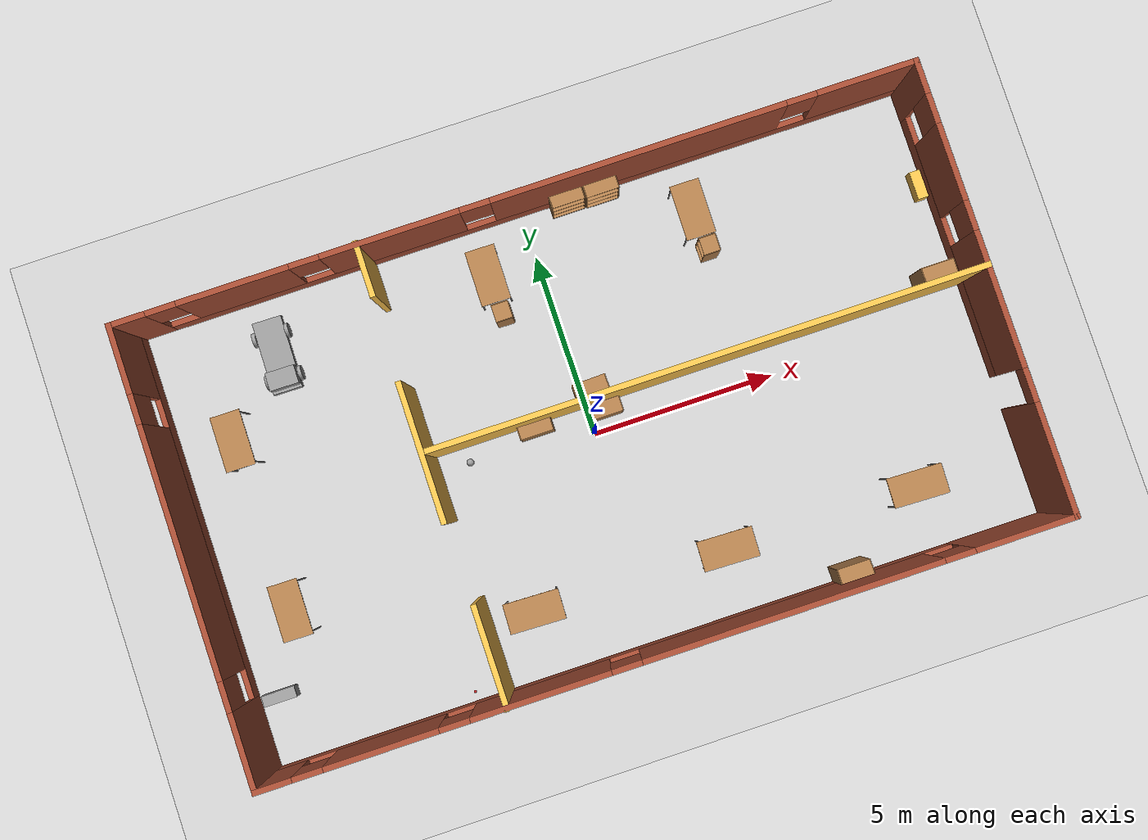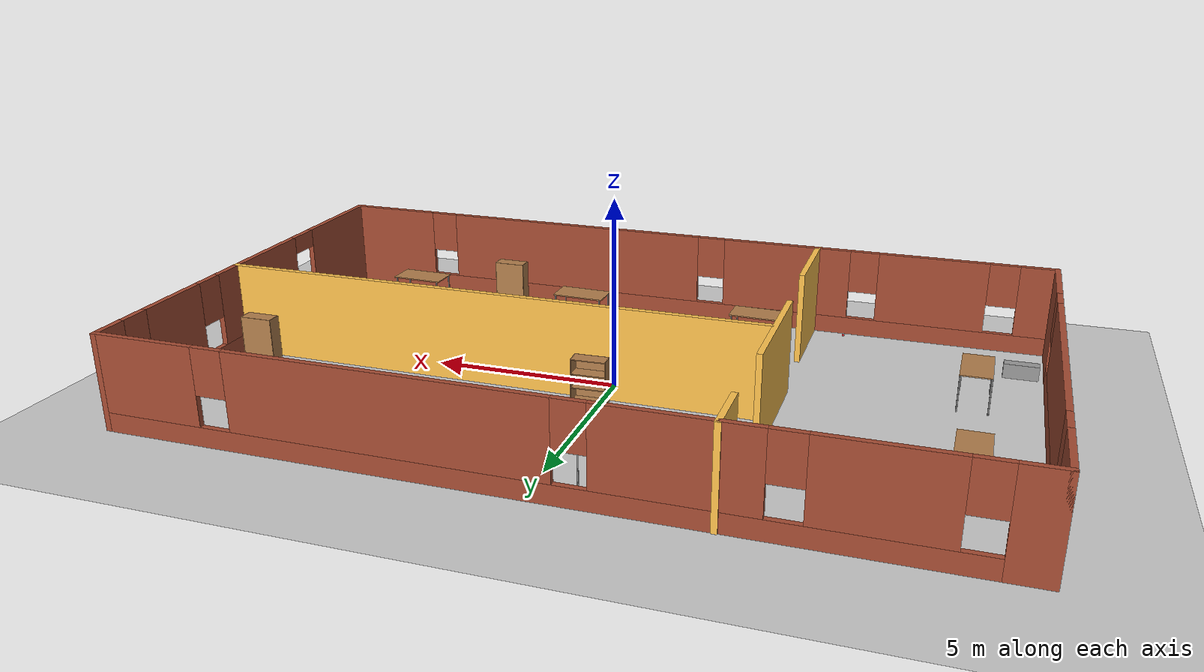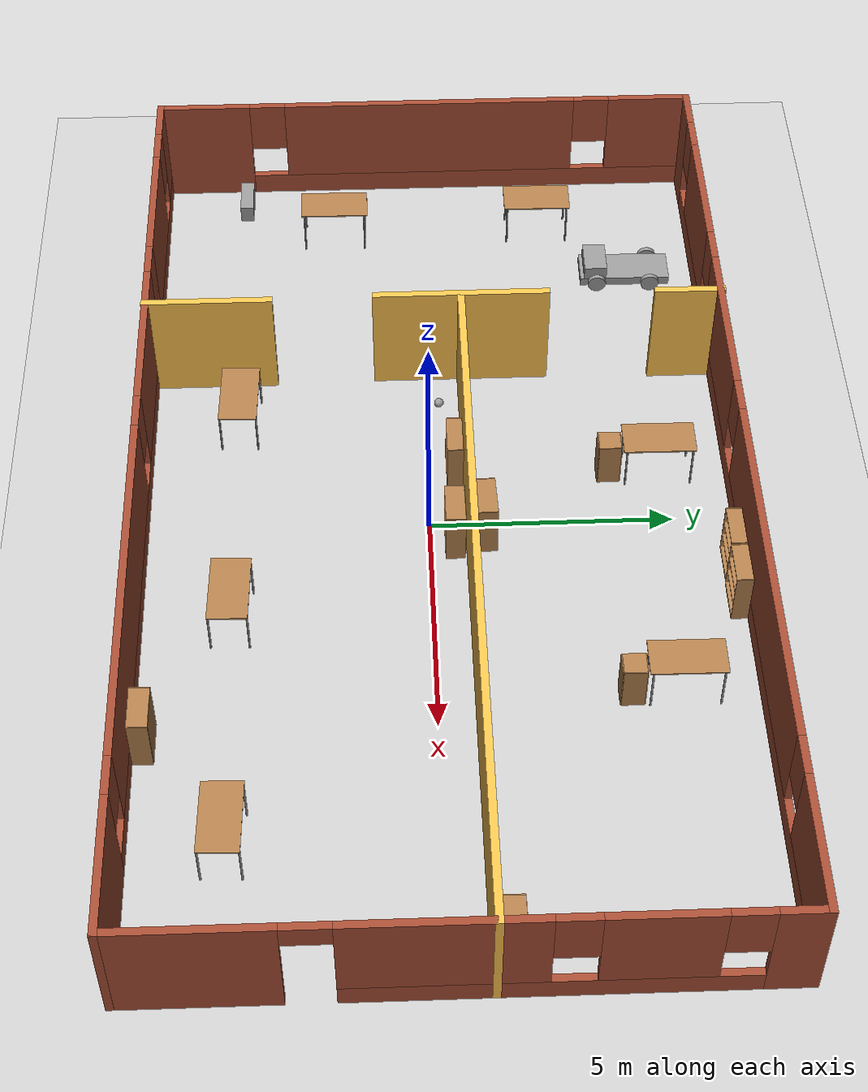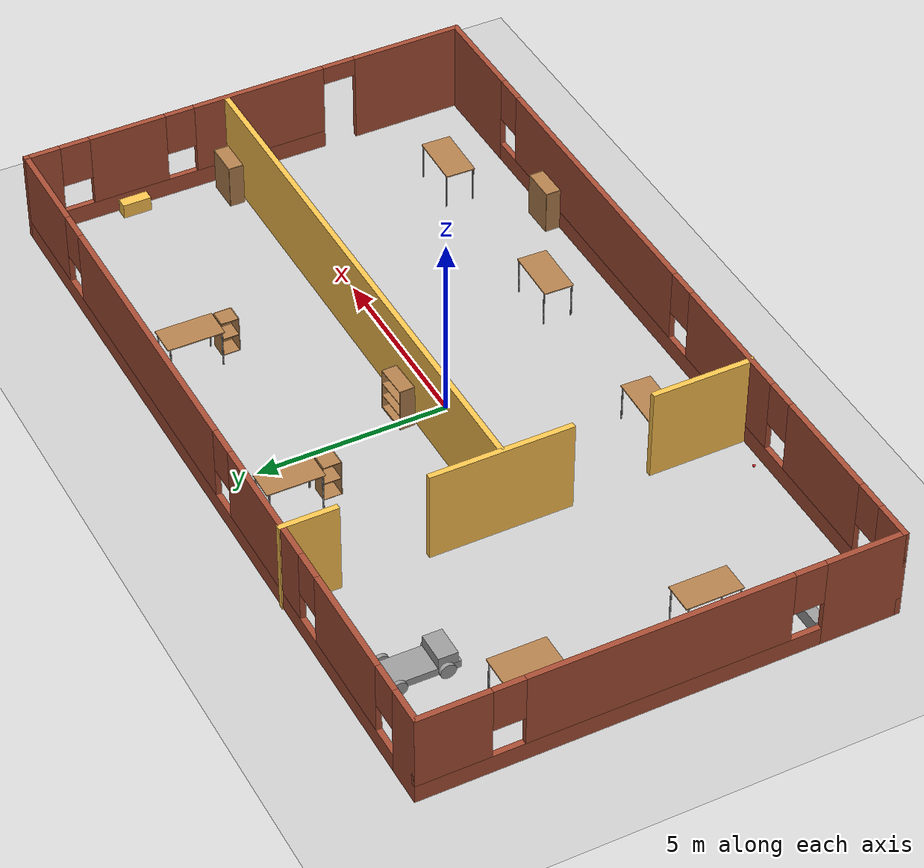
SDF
<sdf version="1.6">
 <world name="default">
  <physics name="default_physics" default="0" type="ode">
   <ode>
    <solver>
     <type>quick</type>
     <iters>50</iters>
     <friction_model>cone_model</friction_model>
     <sor>1.3</sor>
     <use_dynamic_moi_rescaling>0</use_dynamic_moi_rescaling>
    </solver>
    <constraints>
     <cfm>0</cfm>
     <erp>0.2</erp>
     <contact_max_correcting_vel>100</contact_max_correcting_vel>
     <contact_surface_layer>0.001</contact_surface_layer>
    </constraints>
   </ode>
   <max_step_size>0.001</max_step_size>
   <real_time_factor>1</real_time_factor>
   <real_time_update_rate>1000</real_time_update_rate>
  </physics>
  <plugin name="hello" filename="libhello.so"/>
  <light name="sun" type="directional">
   <pose>0 0 10 0 -0 0</pose>
   <diffuse>0.8 0.8 0.8 1</diffuse>
   <specular>0.2 0.2 0.2 1</specular>
   <attenuation>
    <range>1000</range>
    <constant>0.9</constant>
    <linear>0.01</linear>
    <quadratic>0.001</quadratic>
   </attenuation>
   <direction>-0.5 0.1 -0.9</direction>
  </light>
  <model name="ground_plane">
   <static>1</static>
   <link name="link">
    <collision name="collision">
     <geometry><plane><normal>0 0 1</normal><size>100 100</size></plane></geometry>
     <surface><friction><ode><mu>100</mu><mu2>50</mu2></ode></friction></surface>
    </collision>
    <visual name="visual">
     <cast_shadows>0</cast_shadows>
     <geometry><plane><normal>0 0 1</normal><size>100 100</size></plane></geometry>
     <material>
      <script><uri>file://media/materials/scripts/gazebo.material</uri><name>Gazebo/Grey</name></script>
     </material>
    </visual>
   </link>
  </model>
  <gravity>0 0 -9.8</gravity>
  <magnetic_field>6e-06 2.3e-05 -4.2e-05</magnetic_field>
  <atmosphere type="adiabatic"/>
  <physics name="default_physics" default="0" type="ode">
   <max_step_size>0.001</max_step_size>
   <real_time_factor>1</real_time_factor>
   <real_time_update_rate>1000</real_time_update_rate>
  </physics>
  <scene><ambient>0.4 0.4 0.4 1</ambient><background>0.7 0.7 0.7 1</background><shadows>1</shadows></scene>
  <spherical_coordinates>
   <surface_model>EARTH_WGS84</surface_model>
   <latitude_deg>0</latitude_deg>
   <longitude_deg>0</longitude_deg>
   <elevation>0</elevation>
   <heading_deg>0</heading_deg>
  </spherical_coordinates>
  <model name="Building1">
   <pose>-0.03379 0.24138 0 0 -0 0</pose>
   <link name="Wall_0">
    <pose>-0.000989 6.04157 0 0 -0 0</pose>
    <visual name="Wall_0_Visual_0">
     <pose>-10.2395 0 1.25 0 -0 0</pose>
     <geometry><box><size>1.02097 0.15 2.5</size></box></geometry>
     <material>
      <script><uri>file://media/materials/scripts/gazebo.material</uri><name>Gazebo/Bricks</name></script>
      <ambient>1 1 1 1</ambient>
     </material>
     <meta><layer>0</layer></meta>
    </visual>
    <collision name="Wall_0_Collision_0">
     <geometry><box><size>1.02097 0.15 2.5</size></box></geometry>
     <pose>-10.2395 0 1.25 0 -0 0</pose>
    </collision>
    <visual name="Wall_0_Visual_1">
     <pose>0.510485 0 0.25 0 -0 0</pose>
     <geometry><box><size>20.479 0.15 0.5</size></box></geometry>
     <material>
      <script><uri>file://media/materials/scripts/gazebo.material</uri><name>Gazebo/Bricks</name></script>
      <ambient>1 1 1 1</ambient>
     </material>
     <meta><layer>0</layer></meta>
    </visual>
    <collision name="Wall_0_Collision_1">
     <geometry><box><size>20.479 0.15 0.5</size></box></geometry>
     <pose>0.510485 0 0.25 0 -0 0</pose>
    </collision>
    <visual name="Wall_0_Visual_2">
     <pose>-7.44773 0 1.5 0 -0 0</pose>
     <geometry><box><size>2.9626 0.15 2</size></box></geometry>
     <material>
      <script><uri>file://media/materials/scripts/gazebo.material</uri><name>Gazebo/Bricks</name></script>
      <ambient>1 1 1 1</ambient>
     </material>
     <meta><layer>0</layer></meta>
    </visual>
    <collision name="Wall_0_Collision_2">
     <geometry><box><size>2.9626 0.15 2</size></box></geometry>
     <pose>-7.44773 0 1.5 0 -0 0</pose>
    </collision>
    <visual name="Wall_0_Visual_3">
     <pose>-3.31805 0 1.5 0 -0 0</pose>
     <geometry><box><size>3.69676 0.15 2</size></box></geometry>
     <material>
      <script><uri>file://media/materials/scripts/gazebo.material</uri><name>Gazebo/Bricks</name></script>
      <ambient>1 1 1 1</ambient>
     </material>
     <meta><layer>0</layer></meta>
    </visual>
    <collision name="Wall_0_Collision_3">
     <geometry><box><size>3.69676 0.15 2</size></box></geometry>
     <pose>-3.31805 0 1.5 0 -0 0</pose>
    </collision>
    <visual name="Wall_0_Visual_4">
     <pose>3.27414 0 1.5 0 -0 0</pose>
     <geometry><box><size>7.88762 0.15 2</size></box></geometry>
     <material>
      <script><uri>file://media/materials/scripts/gazebo.material</uri><name>Gazebo/Bricks</name></script>
      <ambient>1 1 1 1</ambient>
     </material>
     <meta><layer>0</layer></meta>
    </visual>
    <collision name="Wall_0_Collision_4">
     <geometry><box><size>7.88762 0.15 2</size></box></geometry>
     <pose>3.27414 0 1.5 0 -0 0</pose>
    </collision>
    <visual name="Wall_0_Visual_5">
     <pose>9.38398 0 1.5 0 -0 0</pose>
     <geometry><box><size>2.73204 0.15 2</size></box></geometry>
     <material>
      <script><uri>file://media/materials/scripts/gazebo.material</uri><name>Gazebo/Bricks</name></script>
      <ambient>1 1 1 1</ambient>
     </material>
     <meta><layer>0</layer></meta>
    </visual>
    <collision name="Wall_0_Collision_5">
     <geometry><box><size>2.73204 0.15 2</size></box></geometry>
     <pose>9.38398 0 1.5 0 -0 0</pose>
    </collision>
    <visual name="Wall_0_Visual_6">
     <pose>-9.32903 0 1.9 0 -0 0</pose>
     <geometry><box><size>0.8 0.15 1.2</size></box></geometry>
     <material>
      <script><uri>file://media/materials/scripts/gazebo.material</uri><name>Gazebo/Bricks</name></script>
      <ambient>1 1 1 1</ambient>
     </material>
     <meta><layer>0</layer></meta>
    </visual>
    <collision name="Wall_0_Collision_6">
     <geometry><box><size>0.8 0.15 1.2</size></box></geometry>
     <pose>-9.32903 0 1.9 0 -0 0</pose>
    </collision>
    <visual name="Wall_0_Visual_7">
     <pose>-5.56643 0 1.9 0 -0 0</pose>
     <geometry><box><size>0.8 0.15 1.2</size></box></geometry>
     <material>
      <script><uri>file://media/materials/scripts/gazebo.material</uri><name>Gazebo/Bricks</name></script>
      <ambient>1 1 1 1</ambient>
     </material>
     <meta><layer>0</layer></meta>
    </visual>
    <collision name="Wall_0_Collision_7">
     <geometry><box><size>0.8 0.15 1.2</size></box></geometry>
     <pose>-5.56643 0 1.9 0 -0 0</pose>
    </collision>
    <visual name="Wall_0_Visual_8">
     <pose>-1.06967 0 1.9 0 -0 0</pose>
     <geometry><box><size>0.8 0.15 1.2</size></box></geometry>
     <material>
      <script><uri>file://media/materials/scripts/gazebo.material</uri><name>Gazebo/Bricks</name></script>
      <ambient>1 1 1 1</ambient>
     </material>
     <meta><layer>0</layer></meta>
    </visual>
    <collision name="Wall_0_Collision_8">
     <geometry><box><size>0.8 0.15 1.2</size></box></geometry>
     <pose>-1.06967 0 1.9 0 -0 0</pose>
    </collision>
    <visual name="Wall_0_Visual_9">
     <pose>7.61796 0 1.9 0 -0 0</pose>
     <geometry><box><size>0.8 0.15 1.2</size></box></geometry>
     <material>
      <script><uri>file://media/materials/scripts/gazebo.material</uri><name>Gazebo/Bricks</name></script>
      <ambient>1 1 1 1</ambient>
     </material>
     <meta><layer>0</layer></meta>
    </visual>
    <collision name="Wall_0_Collision_9">
     <geometry><box><size>0.8 0.15 1.2</size></box></geometry>
     <pose>7.61796 0 1.9 0 -0 0</pose>
    </collision>
   </link>
   <link name="Wall_1">
    <pose>10.674 -0.00843 0 0 0 -1.5708</pose>
    <visual name="Wall_1_Visual_0">
     <pose>-5.64511 0 1.25 0 -0 0</pose>
     <geometry><box><size>0.95979 0.15 2.5</size></box></geometry>
     <material>
      <script><uri>file://media/materials/scripts/gazebo.material</uri><name>Gazebo/Bricks</name></script>
      <ambient>1 1 1 1</ambient>
     </material>
     <meta><layer>0</layer></meta>
    </visual>
    <collision name="Wall_1_Collision_0">
     <geometry><box><size>0.95979 0.15 2.5</size></box></geometry>
     <pose>-5.64511 0 1.25 0 -0 0</pose>
    </collision>
    <visual name="Wall_1_Visual_1">
     <pose>4.59102 0 1.25 0 -0 0</pose>
     <geometry><box><size>3.06797 0.15 2.5</size></box></geometry>
     <material>
      <script><uri>file://media/materials/scripts/gazebo.material</uri><name>Gazebo/Bricks</name></script>
      <ambient>1 1 1 1</ambient>
     </material>
     <meta><layer>0</layer></meta>
    </visual>
    <collision name="Wall_1_Collision_1">
     <geometry><box><size>3.06797 0.15 2.5</size></box></geometry>
     <pose>4.59102 0 1.25 0 -0 0</pose>
    </collision>
    <visual name="Wall_1_Visual_2">
     <pose>-1.50409 0 0.25 0 -0 0</pose>
     <geometry><box><size>7.32224 0.15 0.5</size></box></geometry>
     <material>
      <script><uri>file://media/materials/scripts/gazebo.material</uri><name>Gazebo/Bricks</name></script>
      <ambient>1 1 1 1</ambient>
     </material>
     <meta><layer>0</layer></meta>
    </visual>
    <collision name="Wall_1_Collision_2">
     <geometry><box><size>7.32224 0.15 0.5</size></box></geometry>
     <pose>-1.50409 0 0.25 0 -0 0</pose>
    </collision>
    <visual name="Wall_1_Visual_3">
     <pose>-3.32747 0 1.5 0 -0 0</pose>
     <geometry><box><size>2.07548 0.15 2</size></box></geometry>
     <material>
      <script><uri>file://media/materials/scripts/gazebo.material</uri><name>Gazebo/Bricks</name></script>
      <ambient>1 1 1 1</ambient>
     </material>
     <meta><layer>0</layer></meta>
    </visual>
    <collision name="Wall_1_Collision_3">
     <geometry><box><size>2.07548 0.15 2</size></box></geometry>
     <pose>-3.32747 0 1.5 0 -0 0</pose>
    </collision>
    <visual name="Wall_1_Visual_4">
     <pose>0.333653 0 1.5 0 -0 0</pose>
     <geometry><box><size>3.64676 0.15 2</size></box></geometry>
     <material>
      <script><uri>file://media/materials/scripts/gazebo.material</uri><name>Gazebo/Bricks</name></script>
      <ambient>1 1 1 1</ambient>
     </material>
     <meta><layer>0</layer></meta>
    </visual>
    <collision name="Wall_1_Collision_4">
     <geometry><box><size>3.64676 0.15 2</size></box></geometry>
     <pose>0.333653 0 1.5 0 -0 0</pose>
    </collision>
    <visual name="Wall_1_Visual_5">
     <pose>-4.76521 0 1.9 0 -0 0</pose>
     <geometry><box><size>0.8 0.15 1.2</size></box></geometry>
     <material>
      <script><uri>file://media/materials/scripts/gazebo.material</uri><name>Gazebo/Bricks</name></script>
      <ambient>1 1 1 1</ambient>
     </material>
     <meta><layer>0</layer></meta>
    </visual>
    <collision name="Wall_1_Collision_5">
     <geometry><box><size>0.8 0.15 1.2</size></box></geometry>
     <pose>-4.76521 0 1.9 0 -0 0</pose>
    </collision>
    <visual name="Wall_1_Visual_6">
     <pose>-1.88973 0 1.9 0 -0 0</pose>
     <geometry><box><size>0.8 0.15 1.2</size></box></geometry>
     <material>
      <script><uri>file://media/materials/scripts/gazebo.material</uri><name>Gazebo/Bricks</name></script>
      <ambient>1 1 1 1</ambient>
     </material>
     <meta><layer>0</layer></meta>
    </visual>
    <collision name="Wall_1_Collision_6">
     <geometry><box><size>0.8 0.15 1.2</size></box></geometry>
     <pose>-1.88973 0 1.9 0 -0 0</pose>
    </collision>
    <visual name="Wall_1_Visual_7">
     <pose>2.60704 0 2.25 0 -0 0</pose>
     <geometry><box><size>0.9 0.15 0.5</size></box></geometry>
     <material>
      <script><uri>file://media/materials/scripts/gazebo.material</uri><name>Gazebo/Bricks</name></script>
      <ambient>1 1 1 1</ambient>
     </material>
     <meta><layer>0</layer></meta>
    </visual>
    <collision name="Wall_1_Collision_7">
     <geometry><box><size>0.9 0.15 0.5</size></box></geometry>
     <pose>2.60704 0 2.25 0 -0 0</pose>
    </collision>
   </link>
   <link name="Wall_11">
    <collision name="Wall_11_Collision">
     <geometry><box><size>3.75 0.15 2.5</size></box></geometry>
     <pose>0 0 1.25 0 -0 0</pose>
    </collision>
    <visual name="Wall_11_Visual">
     <pose>0 0 1.25 0 -0 0</pose>
     <geometry><box><size>3.75 0.15 2.5</size></box></geometry>
     <material>
      <script><uri>file://media/materials/scripts/gazebo.material</uri><name>Gazebo/Grey</name></script>
      <ambient>1 0.764706 0.305882 1</ambient>
     </material>
     <meta><layer>0</layer></meta>
    </visual>
    <pose>-4.25204 0.570743 0 0 0 -1.5708</pose>
   </link>
   <link name="Wall_13">
    <collision name="Wall_13_Collision">
     <geometry><box><size>2.75 0.15 2.5</size></box></geometry>
     <pose>0 0 1.25 0 -0 0</pose>
    </collision>
    <visual name="Wall_13_Visual">
     <pose>0 0 1.25 0 -0 0</pose>
     <geometry><box><size>2.75 0.15 2.5</size></box></geometry>
     <material>
      <script><uri>file://media/materials/scripts/gazebo.material</uri><name>Gazebo/Grey</name></script>
      <ambient>1 0.764706 0.305882 1</ambient>
     </material>
     <meta><layer>0</layer></meta>
    </visual>
    <pose>-4.19086 -4.77216 0 0 -0 1.5708</pose>
   </link>
   <link name="Wall_15">
    <collision name="Wall_15_Collision">
     <geometry><box><size>1.5 0.15 2.5</size></box></geometry>
     <pose>0 0 1.25 0 -0 0</pose>
    </collision>
    <visual name="Wall_15_Visual">
     <pose>0 0 1.25 0 -0 0</pose>
     <geometry><box><size>1.5 0.15 2.5</size></box></geometry>
     <material>
      <script><uri>file://media/materials/scripts/gazebo.material</uri><name>Gazebo/Grey</name></script>
      <ambient>1 0.764706 0.305882 1</ambient>
     </material>
     <meta><layer>0</layer></meta>
    </visual>
    <pose>-4.19086 5.39716 0 0 0 -1.5708</pose>
   </link>
   <link name="Wall_2">
    <pose>-0.000989 -6.05843 0 0 -0 3.14159</pose>
    <visual name="Wall_2_Visual_0">
     <pose>-9.38398 0 1.25 0 -0 0</pose>
     <geometry><box><size>2.73204 0.15 2.5</size></box></geometry>
     <material>
      <script><uri>file://media/materials/scripts/gazebo.material</uri><name>Gazebo/Bricks</name></script>
      <ambient>1 1 1 1</ambient>
     </material>
     <meta><layer>0</layer></meta>
    </visual>
    <collision name="Wall_2_Collision_0">
     <geometry><box><size>2.73204 0.15 2.5</size></box></geometry>
     <pose>-9.38398 0 1.25 0 -0 0</pose>
    </collision>
    <visual name="Wall_2_Visual_1">
     <pose>1.36602 0 0.25 0 -0 0</pose>
     <geometry><box><size>18.768 0.15 0.5</size></box></geometry>
     <material>
      <script><uri>file://media/materials/scripts/gazebo.material</uri><name>Gazebo/Bricks</name></script>
      <ambient>1 1 1 1</ambient>
     </material>
     <meta><layer>0</layer></meta>
    </visual>
    <collision name="Wall_2_Collision_1">
     <geometry><box><size>18.768 0.15 0.5</size></box></geometry>
     <pose>1.36602 0 0.25 0 -0 0</pose>
    </collision>
    <visual name="Wall_2_Visual_2">
     <pose>-3.27414 0 1.5 0 -0 0</pose>
     <geometry><box><size>7.88762 0.15 2</size></box></geometry>
     <material>
      <script><uri>file://media/materials/scripts/gazebo.material</uri><name>Gazebo/Bricks</name></script>
      <ambient>1 1 1 1</ambient>
     </material>
     <meta><layer>0</layer></meta>
    </visual>
    <collision name="Wall_2_Collision_2">
     <geometry><box><size>7.88762 0.15 2</size></box></geometry>
     <pose>-3.27414 0 1.5 0 -0 0</pose>
    </collision>
    <visual name="Wall_2_Visual_3">
     <pose>3.30275 0 1.5 0 -0 0</pose>
     <geometry><box><size>3.66617 0.15 2</size></box></geometry>
     <material>
      <script><uri>file://media/materials/scripts/gazebo.material</uri><name>Gazebo/Bricks</name></script>
      <ambient>1 1 1 1</ambient>
     </material>
     <meta><layer>0</layer></meta>
    </visual>
    <collision name="Wall_2_Collision_3">
     <geometry><box><size>3.66617 0.15 2</size></box></geometry>
     <pose>3.30275 0 1.5 0 -0 0</pose>
    </collision>
    <visual name="Wall_2_Visual_4">
     <pose>7.43244 0 1.5 0 -0 0</pose>
     <geometry><box><size>2.99319 0.15 2</size></box></geometry>
     <material>
      <script><uri>file://media/materials/scripts/gazebo.material</uri><name>Gazebo/Bricks</name></script>
      <ambient>1 1 1 1</ambient>
     </material>
     <meta><layer>0</layer></meta>
    </visual>
    <collision name="Wall_2_Collision_4">
     <geometry><box><size>2.99319 0.15 2</size></box></geometry>
     <pose>7.43244 0 1.5 0 -0 0</pose>
    </collision>
    <visual name="Wall_2_Visual_5">
     <pose>10.2395 0 1.5 0 -0 0</pose>
     <geometry><box><size>1.02097 0.15 2</size></box></geometry>
     <material>
      <script><uri>file://media/materials/scripts/gazebo.material</uri><name>Gazebo/Bricks</name></script>
      <ambient>1 1 1 1</ambient>
     </material>
     <meta><layer>0</layer></meta>
    </visual>
    <collision name="Wall_2_Collision_5">
     <geometry><box><size>1.02097 0.15 2</size></box></geometry>
     <pose>10.2395 0 1.5 0 -0 0</pose>
    </collision>
    <visual name="Wall_2_Visual_6">
     <pose>-7.61796 0 1.9 0 -0 0</pose>
     <geometry><box><size>0.8 0.15 1.2</size></box></geometry>
     <material>
      <script><uri>file://media/materials/scripts/gazebo.material</uri><name>Gazebo/Bricks</name></script>
      <ambient>1 1 1 1</ambient>
     </material>
     <meta><layer>0</layer></meta>
    </visual>
    <collision name="Wall_2_Collision_6">
     <geometry><box><size>0.8 0.15 1.2</size></box></geometry>
     <pose>-7.61796 0 1.9 0 -0 0</pose>
    </collision>
    <visual name="Wall_2_Visual_7">
     <pose>1.06967 0 1.9 0 -0 0</pose>
     <geometry><box><size>0.8 0.15 1.2</size></box></geometry>
     <material>
      <script><uri>file://media/materials/scripts/gazebo.material</uri><name>Gazebo/Bricks</name></script>
      <ambient>1 1 1 1</ambient>
     </material>
     <meta><layer>0</layer></meta>
    </visual>
    <collision name="Wall_2_Collision_7">
     <geometry><box><size>0.8 0.15 1.2</size></box></geometry>
     <pose>1.06967 0 1.9 0 -0 0</pose>
    </collision>
    <visual name="Wall_2_Visual_8">
     <pose>5.53584 0 1.9 0 -0 0</pose>
     <geometry><box><size>0.8 0.15 1.2</size></box></geometry>
     <material>
      <script><uri>file://media/materials/scripts/gazebo.material</uri><name>Gazebo/Bricks</name></script>
      <ambient>1 1 1 1</ambient>
     </material>
     <meta><layer>0</layer></meta>
    </visual>
    <collision name="Wall_2_Collision_8">
     <geometry><box><size>0.8 0.15 1.2</size></box></geometry>
     <pose>5.53584 0 1.9 0 -0 0</pose>
    </collision>
    <visual name="Wall_2_Visual_9">
     <pose>9.32903 0 1.9 0 -0 0</pose>
     <geometry><box><size>0.8 0.15 1.2</size></box></geometry>
     <material>
      <script><uri>file://media/materials/scripts/gazebo.material</uri><name>Gazebo/Bricks</name></script>
      <ambient>1 1 1 1</ambient>
     </material>
     <meta><layer>0</layer></meta>
    </visual>
    <collision name="Wall_2_Collision_9">
     <geometry><box><size>0.8 0.15 1.2</size></box></geometry>
     <pose>9.32903 0 1.9 0 -0 0</pose>
    </collision>
   </link>
   <link name="Wall_3">
    <pose>-10.676 -0.00843 0 0 -0 1.5708</pose>
    <visual name="Wall_3_Visual_0">
     <pose>-5.07076 0 1.25 0 -0 0</pose>
     <geometry><box><size>2.10849 0.15 2.5</size></box></geometry>
     <material>
      <script><uri>file://media/materials/scripts/gazebo.material</uri><name>Gazebo/Bricks</name></script>
      <ambient>1 1 1 1</ambient>
     </material>
     <meta><layer>0</layer></meta>
    </visual>
    <collision name="Wall_3_Collision_0">
     <geometry><box><size>2.10849 0.15 2.5</size></box></geometry>
     <pose>-5.07076 0 1.25 0 -0 0</pose>
    </collision>
    <visual name="Wall_3_Visual_1">
     <pose>1.05424 0 0.25 0 -0 0</pose>
     <geometry><box><size>10.1415 0.15 0.5</size></box></geometry>
     <material>
      <script><uri>file://media/materials/scripts/gazebo.material</uri><name>Gazebo/Bricks</name></script>
      <ambient>1 1 1 1</ambient>
     </material>
     <meta><layer>0</layer></meta>
    </visual>
    <collision name="Wall_3_Collision_1">
     <geometry><box><size>10.1415 0.15 0.5</size></box></geometry>
     <pose>1.05424 0 0.25 0 -0 0</pose>
    </collision>
    <visual name="Wall_3_Visual_2">
     <pose>0.115496 0 1.5 0 -0 0</pose>
     <geometry><box><size>6.66402 0.15 2</size></box></geometry>
     <material>
      <script><uri>file://media/materials/scripts/gazebo.material</uri><name>Gazebo/Bricks</name></script>
      <ambient>1 1 1 1</ambient>
     </material>
     <meta><layer>0</layer></meta>
    </visual>
    <collision name="Wall_3_Collision_2">
     <geometry><box><size>6.66402 0.15 2</size></box></geometry>
     <pose>0.115496 0 1.5 0 -0 0</pose>
    </collision>
    <visual name="Wall_3_Visual_3">
     <pose>5.18625 0 1.5 0 -0 0</pose>
     <geometry><box><size>1.8775 0.15 2</size></box></geometry>
     <material>
      <script><uri>file://media/materials/scripts/gazebo.material</uri><name>Gazebo/Bricks</name></script>
      <ambient>1 1 1 1</ambient>
     </material>
     <meta><layer>0</layer></meta>
    </visual>
    <collision name="Wall_3_Collision_3">
     <geometry><box><size>1.8775 0.15 2</size></box></geometry>
     <pose>5.18625 0 1.5 0 -0 0</pose>
    </collision>
    <visual name="Wall_3_Visual_4">
     <pose>-3.61651 0 1.9 0 -0 0</pose>
     <geometry><box><size>0.8 0.15 1.2</size></box></geometry>
     <material>
      <script><uri>file://media/materials/scripts/gazebo.material</uri><name>Gazebo/Bricks</name></script>
      <ambient>1 1 1 1</ambient>
     </material>
     <meta><layer>0</layer></meta>
    </visual>
    <collision name="Wall_3_Collision_4">
     <geometry><box><size>0.8 0.15 1.2</size></box></geometry>
     <pose>-3.61651 0 1.9 0 -0 0</pose>
    </collision>
    <visual name="Wall_3_Visual_5">
     <pose>3.8475 0 1.9 0 -0 0</pose>
     <geometry><box><size>0.8 0.15 1.2</size></box></geometry>
     <material>
      <script><uri>file://media/materials/scripts/gazebo.material</uri><name>Gazebo/Bricks</name></script>
      <ambient>1 1 1 1</ambient>
     </material>
     <meta><layer>0</layer></meta>
    </visual>
    <collision name="Wall_3_Collision_5">
     <geometry><box><size>0.8 0.15 1.2</size></box></geometry>
     <pose>3.8475 0 1.9 0 -0 0</pose>
    </collision>
   </link>
   <link name="Wall_9">
    <collision name="Wall_9_Collision">
     <geometry><box><size>15 0.15 2.5</size></box></geometry>
     <pose>0 0 1.25 0 -0 0</pose>
    </collision>
    <visual name="Wall_9_Visual">
     <pose>0 0 1.25 0 -0 0</pose>
     <geometry><box><size>15 0.15 2.5</size></box></geometry>
     <material>
      <script><uri>file://media/materials/scripts/gazebo.material</uri><name>Gazebo/Grey</name></script>
      <ambient>1 0.764706 0.305882 1</ambient>
     </material>
     <meta><layer>0</layer></meta>
    </visual>
    <pose>3.25099 0.565919 0 0 -0 3.14159</pose>
   </link>
   <static>1</static>
  </model>
  <model name="bookshelf">
   <static>1</static>
   <link name="link">
    <inertial><mass>1</mass></inertial>
    <collision name="back">
     <pose>0 0.005 0.6 0 -0 0</pose>
     <geometry><box><size>0.9 0.01 1.2</size></box></geometry>
    </collision>
    <visual name="visual1">
     <pose>0 0.005 0.6 0 -0 0</pose>
     <geometry><box><size>0.9 0.01 1.2</size></box></geometry>
     <material>
      <script><uri>file://media/materials/scripts/gazebo.material</uri><name>Gazebo/Wood</name></script>
     </material>
    </visual>
    <collision name="left_side">
     <pose>0.45 -0.195 0.6 0 -0 0</pose>
     <geometry><box><size>0.02 0.4 1.2</size></box></geometry>
    </collision>
    <visual name="visual2">
     <pose>0.45 -0.195 0.6 0 -0 0</pose>
     <geometry><box><size>0.02 0.4 1.2</size></box></geometry>
     <material>
      <script><uri>file://media/materials/scripts/gazebo.material</uri><name>Gazebo/Wood</name></script>
     </material>
    </visual>
    <collision name="right_side">
     <pose>-0.45 -0.195 0.6 0 -0 0</pose>
     <geometry><box><size>0.02 0.4 1.2</size></box></geometry>
    </collision>
    <visual name="visual3">
     <pose>-0.45 -0.195 0.6 0 -0 0</pose>
     <geometry><box><size>0.02 0.4 1.2</size></box></geometry>
     <material>
      <script><uri>file://media/materials/scripts/gazebo.material</uri><name>Gazebo/Wood</name></script>
     </material>
    </visual>
    <collision name="bottom">
     <pose>0 -0.195 0.03 0 -0 0</pose>
     <geometry><box><size>0.88 0.4 0.06</size></box></geometry>
    </collision>
    <visual name="visual4">
     <pose>0 -0.195 0.03 0 -0 0</pose>
     <geometry><box><size>0.88 0.4 0.06</size></box></geometry>
     <material>
      <script><uri>file://media/materials/scripts/gazebo.material</uri><name>Gazebo/Wood</name></script>
     </material>
    </visual>
    <collision name="top">
     <pose>0 -0.195 1.19 0 -0 0</pose>
     <geometry><box><size>0.88 0.4 0.02</size></box></geometry>
    </collision>
    <visual name="visual5">
     <pose>0 -0.195 1.19 0 -0 0</pose>
     <geometry><box><size>0.88 0.4 0.02</size></box></geometry>
     <material>
      <script><uri>file://media/materials/scripts/gazebo.material</uri><name>Gazebo/Wood</name></script>
     </material>
    </visual>
    <collision name="low_shelf">
     <pose>0 -0.195 0.43 0 -0 0</pose>
     <geometry><box><size>0.88 0.4 0.02</size></box></geometry>
    </collision>
    <visual name="visual6">
     <pose>0 -0.195 0.43 0 -0 0</pose>
     <geometry><box><size>0.88 0.4 0.02</size></box></geometry>
     <material>
      <script><uri>file://media/materials/scripts/gazebo.material</uri><name>Gazebo/Wood</name></script>
     </material>
    </visual>
    <collision name="high_shelf">
     <pose>0 -0.195 0.8 0 -0 0</pose>
     <geometry><box><size>0.88 0.4 0.02</size></box></geometry>
    </collision>
    <visual name="visual7">
     <pose>0 -0.195 0.8 0 -0 0</pose>
     <geometry><box><size>0.88 0.4 0.02</size></box></geometry>
     <material>
      <script><uri>file://media/materials/scripts/gazebo.material</uri><name>Gazebo/Wood</name></script>
     </material>
    </visual>
   </link>
   <pose>1.2383 6.28205 0 0 -0 0</pose>
  </model>
  <model name="bookshelf_0">
   <static>1</static>
   <link name="link">
    <inertial><mass>1</mass></inertial>
    <collision name="back">
     <pose>0 0.005 0.6 0 -0 0</pose>
     <geometry><box><size>0.9 0.01 1.2</size></box></geometry>
    </collision>
    <visual name="visual1">
     <pose>0 0.005 0.6 0 -0 0</pose>
     <geometry><box><size>0.9 0.01 1.2</size></box></geometry>
     <material>
      <script><uri>file://media/materials/scripts/gazebo.material</uri><name>Gazebo/Wood</name></script>
     </material>
    </visual>
    <collision name="left_side">
     <pose>0.45 -0.195 0.6 0 -0 0</pose>
     <geometry><box><size>0.02 0.4 1.2</size></box></geometry>
    </collision>
    <visual name="visual2">
     <pose>0.45 -0.195 0.6 0 -0 0</pose>
     <geometry><box><size>0.02 0.4 1.2</size></box></geometry>
     <material>
      <script><uri>file://media/materials/scripts/gazebo.material</uri><name>Gazebo/Wood</name></script>
     </material>
    </visual>
    <collision name="right_side">
     <pose>-0.45 -0.195 0.6 0 -0 0</pose>
     <geometry><box><size>0.02 0.4 1.2</size></box></geometry>
    </collision>
    <visual name="visual3">
     <pose>-0.45 -0.195 0.6 0 -0 0</pose>
     <geometry><box><size>0.02 0.4 1.2</size></box></geometry>
     <material>
      <script><uri>file://media/materials/scripts/gazebo.material</uri><name>Gazebo/Wood</name></script>
     </material>
    </visual>
    <collision name="bottom">
     <pose>0 -0.195 0.03 0 -0 0</pose>
     <geometry><box><size>0.88 0.4 0.06</size></box></geometry>
    </collision>
    <visual name="visual4">
     <pose>0 -0.195 0.03 0 -0 0</pose>
     <geometry><box><size>0.88 0.4 0.06</size></box></geometry>
     <material>
      <script><uri>file://media/materials/scripts/gazebo.material</uri><name>Gazebo/Wood</name></script>
     </material>
    </visual>
    <collision name="top">
     <pose>0 -0.195 1.19 0 -0 0</pose>
     <geometry><box><size>0.88 0.4 0.02</size></box></geometry>
    </collision>
    <visual name="visual5">
     <pose>0 -0.195 1.19 0 -0 0</pose>
     <geometry><box><size>0.88 0.4 0.02</size></box></geometry>
     <material>
      <script><uri>file://media/materials/scripts/gazebo.material</uri><name>Gazebo/Wood</name></script>
     </material>
    </visual>
    <collision name="low_shelf">
     <pose>0 -0.195 0.43 0 -0 0</pose>
     <geometry><box><size>0.88 0.4 0.02</size></box></geometry>
    </collision>
    <visual name="visual6">
     <pose>0 -0.195 0.43 0 -0 0</pose>
     <geometry><box><size>0.88 0.4 0.02</size></box></geometry>
     <material>
      <script><uri>file://media/materials/scripts/gazebo.material</uri><name>Gazebo/Wood</name></script>
     </material>
    </visual>
    <collision name="high_shelf">
     <pose>0 -0.195 0.8 0 -0 0</pose>
     <geometry><box><size>0.88 0.4 0.02</size></box></geometry>
    </collision>
    <visual name="visual7">
     <pose>0 -0.195 0.8 0 -0 0</pose>
     <geometry><box><size>0.88 0.4 0.02</size></box></geometry>
     <material>
      <script><uri>file://media/materials/scripts/gazebo.material</uri><name>Gazebo/Wood</name></script>
     </material>
    </visual>
   </link>
   <pose>2.17717 6.2674 0 0 -0 0</pose>
  </model>
  <model name="table">
   <static>1</static>
   <link name="link">
    <collision name="surface">
     <pose>0 0 1 0 -0 0</pose>
     <geometry><box><size>1.5 0.8 0.03</size></box></geometry>
     <surface><friction><ode><mu>0.6</mu><mu2>0.6</mu2></ode></friction></surface>
    </collision>
    <visual name="visual1">
     <pose>0 0 1 0 -0 0</pose>
     <geometry><box><size>1.5 0.8 0.03</size></box></geometry>
     <material>
      <script><uri>file://media/materials/scripts/gazebo.material</uri><name>Gazebo/Wood</name></script>
     </material>
    </visual>
    <collision name="front_left_leg">
     <pose>0.68 0.38 0.5 0 -0 0</pose>
     <geometry><cylinder><radius>0.02</radius><length>1</length></cylinder></geometry>
    </collision>
    <visual name="front_left_leg">
     <pose>0.68 0.38 0.5 0 -0 0</pose>
     <geometry><cylinder><radius>0.02</radius><length>1</length></cylinder></geometry>
     <material>
      <script><uri>file://media/materials/scripts/gazebo.material</uri><name>Gazebo/Grey</name></script>
     </material>
    </visual>
    <collision name="front_right_leg">
     <pose>0.68 -0.38 0.5 0 -0 0</pose>
     <geometry><cylinder><radius>0.02</radius><length>1</length></cylinder></geometry>
    </collision>
    <visual name="front_right_leg">
     <pose>0.68 -0.38 0.5 0 -0 0</pose>
     <geometry><cylinder><radius>0.02</radius><length>1</length></cylinder></geometry>
     <material>
      <script><uri>file://media/materials/scripts/gazebo.material</uri><name>Gazebo/Grey</name></script>
     </material>
    </visual>
    <collision name="back_right_leg">
     <pose>-0.68 -0.38 0.5 0 -0 0</pose>
     <geometry><cylinder><radius>0.02</radius><length>1</length></cylinder></geometry>
    </collision>
    <visual name="back_right_leg">
     <pose>-0.68 -0.38 0.5 0 -0 0</pose>
     <geometry><cylinder><radius>0.02</radius><length>1</length></cylinder></geometry>
     <material>
      <script><uri>file://media/materials/scripts/gazebo.material</uri><name>Gazebo/Grey</name></script>
     </material>
    </visual>
    <collision name="back_left_leg">
     <pose>-0.68 0.38 0.5 0 -0 0</pose>
     <geometry><cylinder><radius>0.02</radius><length>1</length></cylinder></geometry>
    </collision>
    <visual name="back_left_leg">
     <pose>-0.68 0.38 0.5 0 -0 0</pose>
     <geometry><cylinder><radius>0.02</radius><length>1</length></cylinder></geometry>
     <material>
      <script><uri>file://media/materials/scripts/gazebo.material</uri><name>Gazebo/Grey</name></script>
     </material>
    </visual>
   </link>
   <pose>-1.36641 4.79092 0 0 0 -1.57662</pose>
  </model>
  <model name="table_clone">
   <static>1</static>
   <link name="link">
    <collision name="surface">
     <pose>0 0 1 0 -0 0</pose>
     <geometry><box><size>1.5 0.8 0.03</size></box></geometry>
     <surface><friction><ode><mu>0.6</mu><mu2>0.6</mu2></ode></friction></surface>
    </collision>
    <visual name="visual1">
     <pose>0 0 1 0 -0 0</pose>
     <geometry><box><size>1.5 0.8 0.03</size></box></geometry>
     <material>
      <script><uri>file://media/materials/scripts/gazebo.material</uri><name>Gazebo/Wood</name></script>
     </material>
    </visual>
    <collision name="front_left_leg">
     <pose>0.68 0.38 0.5 0 -0 0</pose>
     <geometry><cylinder><radius>0.02</radius><length>1</length></cylinder></geometry>
    </collision>
    <visual name="front_left_leg">
     <pose>0.68 0.38 0.5 0 -0 0</pose>
     <geometry><cylinder><radius>0.02</radius><length>1</length></cylinder></geometry>
     <material>
      <script><uri>file://media/materials/scripts/gazebo.material</uri><name>Gazebo/Grey</name></script>
     </material>
    </visual>
    <collision name="front_right_leg">
     <pose>0.68 -0.38 0.5 0 -0 0</pose>
     <geometry><cylinder><radius>0.02</radius><length>1</length></cylinder></geometry>
    </collision>
    <visual name="front_right_leg">
     <pose>0.68 -0.38 0.5 0 -0 0</pose>
     <geometry><cylinder><radius>0.02</radius><length>1</length></cylinder></geometry>
     <material>
      <script><uri>file://media/materials/scripts/gazebo.material</uri><name>Gazebo/Grey</name></script>
     </material>
    </visual>
    <collision name="back_right_leg">
     <pose>-0.68 -0.38 0.5 0 -0 0</pose>
     <geometry><cylinder><radius>0.02</radius><length>1</length></cylinder></geometry>
    </collision>
    <visual name="back_right_leg">
     <pose>-0.68 -0.38 0.5 0 -0 0</pose>
     <geometry><cylinder><radius>0.02</radius><length>1</length></cylinder></geometry>
     <material>
      <script><uri>file://media/materials/scripts/gazebo.material</uri><name>Gazebo/Grey</name></script>
     </material>
    </visual>
    <collision name="back_left_leg">
     <pose>-0.68 0.38 0.5 0 -0 0</pose>
     <geometry><cylinder><radius>0.02</radius><length>1</length></cylinder></geometry>
    </collision>
    <visual name="back_left_leg">
     <pose>-0.68 0.38 0.5 0 -0 0</pose>
     <geometry><cylinder><radius>0.02</radius><length>1</length></cylinder></geometry>
     <material>
      <script><uri>file://media/materials/scripts/gazebo.material</uri><name>Gazebo/Grey</name></script>
     </material>
    </visual>
   </link>
   <pose>4.28955 4.75152 0 0 0 -1.57662</pose>
  </model>
  <model name="table_clone_clone">
   <static>1</static>
   <link name="link">
    <collision name="surface">
     <pose>0 0 1 0 -0 0</pose>
     <geometry><box><size>1.5 0.8 0.03</size></box></geometry>
     <surface><friction><ode><mu>0.6</mu><mu2>0.6</mu2></ode></friction></surface>
    </collision>
    <visual name="visual1">
     <pose>0 0 1 0 -0 0</pose>
     <geometry><box><size>1.5 0.8 0.03</size></box></geometry>
     <material>
      <script><uri>file://media/materials/scripts/gazebo.material</uri><name>Gazebo/Wood</name></script>
     </material>
    </visual>
    <collision name="front_left_leg">
     <pose>0.68 0.38 0.5 0 -0 0</pose>
     <geometry><cylinder><radius>0.02</radius><length>1</length></cylinder></geometry>
    </collision>
    <visual name="front_left_leg">
     <pose>0.68 0.38 0.5 0 -0 0</pose>
     <geometry><cylinder><radius>0.02</radius><length>1</length></cylinder></geometry>
     <material>
      <script><uri>file://media/materials/scripts/gazebo.material</uri><name>Gazebo/Grey</name></script>
     </material>
    </visual>
    <collision name="front_right_leg">
     <pose>0.68 -0.38 0.5 0 -0 0</pose>
     <geometry><cylinder><radius>0.02</radius><length>1</length></cylinder></geometry>
    </collision>
    <visual name="front_right_leg">
     <pose>0.68 -0.38 0.5 0 -0 0</pose>
     <geometry><cylinder><radius>0.02</radius><length>1</length></cylinder></geometry>
     <material>
      <script><uri>file://media/materials/scripts/gazebo.material</uri><name>Gazebo/Grey</name></script>
     </material>
    </visual>
    <collision name="back_right_leg">
     <pose>-0.68 -0.38 0.5 0 -0 0</pose>
     <geometry><cylinder><radius>0.02</radius><length>1</length></cylinder></geometry>
    </collision>
    <visual name="back_right_leg">
     <pose>-0.68 -0.38 0.5 0 -0 0</pose>
     <geometry><cylinder><radius>0.02</radius><length>1</length></cylinder></geometry>
     <material>
      <script><uri>file://media/materials/scripts/gazebo.material</uri><name>Gazebo/Grey</name></script>
     </material>
    </visual>
    <collision name="back_left_leg">
     <pose>-0.68 0.38 0.5 0 -0 0</pose>
     <geometry><cylinder><radius>0.02</radius><length>1</length></cylinder></geometry>
    </collision>
    <visual name="back_left_leg">
     <pose>-0.68 0.38 0.5 0 -0 0</pose>
     <geometry><cylinder><radius>0.02</radius><length>1</length></cylinder></geometry>
     <material>
      <script><uri>file://media/materials/scripts/gazebo.material</uri><name>Gazebo/Grey</name></script>
     </material>
    </visual>
   </link>
   <pose>-2.95006 -3.9138 0 0 -0 3.11071</pose>
  </model>
  <model name="table_clone_clone_clone">
   <static>1</static>
   <link name="link">
    <collision name="surface">
     <pose>0 0 1 0 -0 0</pose>
     <geometry><box><size>1.5 0.8 0.03</size></box></geometry>
     <surface><friction><ode><mu>0.6</mu><mu2>0.6</mu2></ode></friction></surface>
    </collision>
    <visual name="visual1">
     <pose>0 0 1 0 -0 0</pose>
     <geometry><box><size>1.5 0.8 0.03</size></box></geometry>
     <material>
      <script><uri>file://media/materials/scripts/gazebo.material</uri><name>Gazebo/Wood</name></script>
     </material>
    </visual>
    <collision name="front_left_leg">
     <pose>0.68 0.38 0.5 0 -0 0</pose>
     <geometry><cylinder><radius>0.02</radius><length>1</length></cylinder></geometry>
    </collision>
    <visual name="front_left_leg">
     <pose>0.68 0.38 0.5 0 -0 0</pose>
     <geometry><cylinder><radius>0.02</radius><length>1</length></cylinder></geometry>
     <material>
      <script><uri>file://media/materials/scripts/gazebo.material</uri><name>Gazebo/Grey</name></script>
     </material>
    </visual>
    <collision name="front_right_leg">
     <pose>0.68 -0.38 0.5 0 -0 0</pose>
     <geometry><cylinder><radius>0.02</radius><length>1</length></cylinder></geometry>
    </collision>
    <visual name="front_right_leg">
     <pose>0.68 -0.38 0.5 0 -0 0</pose>
     <geometry><cylinder><radius>0.02</radius><length>1</length></cylinder></geometry>
     <material>
      <script><uri>file://media/materials/scripts/gazebo.material</uri><name>Gazebo/Grey</name></script>
     </material>
    </visual>
    <collision name="back_right_leg">
     <pose>-0.68 -0.38 0.5 0 -0 0</pose>
     <geometry><cylinder><radius>0.02</radius><length>1</length></cylinder></geometry>
    </collision>
    <visual name="back_right_leg">
     <pose>-0.68 -0.38 0.5 0 -0 0</pose>
     <geometry><cylinder><radius>0.02</radius><length>1</length></cylinder></geometry>
     <material>
      <script><uri>file://media/materials/scripts/gazebo.material</uri><name>Gazebo/Grey</name></script>
     </material>
    </visual>
    <collision name="back_left_leg">
     <pose>-0.68 0.38 0.5 0 -0 0</pose>
     <geometry><cylinder><radius>0.02</radius><length>1</length></cylinder></geometry>
    </collision>
    <visual name="back_left_leg">
     <pose>-0.68 0.38 0.5 0 -0 0</pose>
     <geometry><cylinder><radius>0.02</radius><length>1</length></cylinder></geometry>
     <material>
      <script><uri>file://media/materials/scripts/gazebo.material</uri><name>Gazebo/Grey</name></script>
     </material>
    </visual>
   </link>
   <pose>2.31941 -3.96963 0 0 -0 3.11071</pose>
  </model>
  <model name="bookshelf_clone">
   <static>1</static>
   <link name="link">
    <inertial><mass>1</mass></inertial>
    <collision name="back">
     <pose>0 0.005 0.6 0 -0 0</pose>
     <geometry><box><size>0.9 0.01 1.2</size></box></geometry>
    </collision>
    <visual name="visual1">
     <pose>0 0.005 0.6 0 -0 0</pose>
     <geometry><box><size>0.9 0.01 1.2</size></box></geometry>
     <material>
      <script><uri>file://media/materials/scripts/gazebo.material</uri><name>Gazebo/Wood</name></script>
     </material>
    </visual>
    <collision name="left_side">
     <pose>0.45 -0.195 0.6 0 -0 0</pose>
     <geometry><box><size>0.02 0.4 1.2</size></box></geometry>
    </collision>
    <visual name="visual2">
     <pose>0.45 -0.195 0.6 0 -0 0</pose>
     <geometry><box><size>0.02 0.4 1.2</size></box></geometry>
     <material>
      <script><uri>file://media/materials/scripts/gazebo.material</uri><name>Gazebo/Wood</name></script>
     </material>
    </visual>
    <collision name="right_side">
     <pose>-0.45 -0.195 0.6 0 -0 0</pose>
     <geometry><box><size>0.02 0.4 1.2</size></box></geometry>
    </collision>
    <visual name="visual3">
     <pose>-0.45 -0.195 0.6 0 -0 0</pose>
     <geometry><box><size>0.02 0.4 1.2</size></box></geometry>
     <material>
      <script><uri>file://media/materials/scripts/gazebo.material</uri><name>Gazebo/Wood</name></script>
     </material>
    </visual>
    <collision name="bottom">
     <pose>0 -0.195 0.03 0 -0 0</pose>
     <geometry><box><size>0.88 0.4 0.06</size></box></geometry>
    </collision>
    <visual name="visual4">
     <pose>0 -0.195 0.03 0 -0 0</pose>
     <geometry><box><size>0.88 0.4 0.06</size></box></geometry>
     <material>
      <script><uri>file://media/materials/scripts/gazebo.material</uri><name>Gazebo/Wood</name></script>
     </material>
    </visual>
    <collision name="top">
     <pose>0 -0.195 1.19 0 -0 0</pose>
     <geometry><box><size>0.88 0.4 0.02</size></box></geometry>
    </collision>
    <visual name="visual5">
     <pose>0 -0.195 1.19 0 -0 0</pose>
     <geometry><box><size>0.88 0.4 0.02</size></box></geometry>
     <material>
      <script><uri>file://media/materials/scripts/gazebo.material</uri><name>Gazebo/Wood</name></script>
     </material>
    </visual>
    <collision name="low_shelf">
     <pose>0 -0.195 0.43 0 -0 0</pose>
     <geometry><box><size>0.88 0.4 0.02</size></box></geometry>
    </collision>
    <visual name="visual6">
     <pose>0 -0.195 0.43 0 -0 0</pose>
     <geometry><box><size>0.88 0.4 0.02</size></box></geometry>
     <material>
      <script><uri>file://media/materials/scripts/gazebo.material</uri><name>Gazebo/Wood</name></script>
     </material>
    </visual>
    <collision name="high_shelf">
     <pose>0 -0.195 0.8 0 -0 0</pose>
     <geometry><box><size>0.88 0.4 0.02</size></box></geometry>
    </collision>
    <visual name="visual7">
     <pose>0 -0.195 0.8 0 -0 0</pose>
     <geometry><box><size>0.88 0.4 0.02</size></box></geometry>
     <material>
      <script><uri>file://media/materials/scripts/gazebo.material</uri><name>Gazebo/Wood</name></script>
     </material>
    </visual>
   </link>
   <pose>-1.43926 0.795295 0 0 -0 0</pose>
  </model>
  <model name="bookshelf_clone_0">
   <static>1</static>
   <link name="link">
    <inertial><mass>1</mass></inertial>
    <collision name="back">
     <pose>0 0.005 0.6 0 -0 0</pose>
     <geometry><box><size>0.9 0.01 1.2</size></box></geometry>
    </collision>
    <visual name="visual1">
     <pose>0 0.005 0.6 0 -0 0</pose>
     <geometry><box><size>0.9 0.01 1.2</size></box></geometry>
     <material>
      <script><uri>file://media/materials/scripts/gazebo.material</uri><name>Gazebo/Wood</name></script>
     </material>
    </visual>
    <collision name="left_side">
     <pose>0.45 -0.195 0.6 0 -0 0</pose>
     <geometry><box><size>0.02 0.4 1.2</size></box></geometry>
    </collision>
    <visual name="visual2">
     <pose>0.45 -0.195 0.6 0 -0 0</pose>
     <geometry><box><size>0.02 0.4 1.2</size></box></geometry>
     <material>
      <script><uri>file://media/materials/scripts/gazebo.material</uri><name>Gazebo/Wood</name></script>
     </material>
    </visual>
    <collision name="right_side">
     <pose>-0.45 -0.195 0.6 0 -0 0</pose>
     <geometry><box><size>0.02 0.4 1.2</size></box></geometry>
    </collision>
    <visual name="visual3">
     <pose>-0.45 -0.195 0.6 0 -0 0</pose>
     <geometry><box><size>0.02 0.4 1.2</size></box></geometry>
     <material>
      <script><uri>file://media/materials/scripts/gazebo.material</uri><name>Gazebo/Wood</name></script>
     </material>
    </visual>
    <collision name="bottom">
     <pose>0 -0.195 0.03 0 -0 0</pose>
     <geometry><box><size>0.88 0.4 0.06</size></box></geometry>
    </collision>
    <visual name="visual4">
     <pose>0 -0.195 0.03 0 -0 0</pose>
     <geometry><box><size>0.88 0.4 0.06</size></box></geometry>
     <material>
      <script><uri>file://media/materials/scripts/gazebo.material</uri><name>Gazebo/Wood</name></script>
     </material>
    </visual>
    <collision name="top">
     <pose>0 -0.195 1.19 0 -0 0</pose>
     <geometry><box><size>0.88 0.4 0.02</size></box></geometry>
    </collision>
    <visual name="visual5">
     <pose>0 -0.195 1.19 0 -0 0</pose>
     <geometry><box><size>0.88 0.4 0.02</size></box></geometry>
     <material>
      <script><uri>file://media/materials/scripts/gazebo.material</uri><name>Gazebo/Wood</name></script>
     </material>
    </visual>
    <collision name="low_shelf">
     <pose>0 -0.195 0.43 0 -0 0</pose>
     <geometry><box><size>0.88 0.4 0.02</size></box></geometry>
    </collision>
    <visual name="visual6">
     <pose>0 -0.195 0.43 0 -0 0</pose>
     <geometry><box><size>0.88 0.4 0.02</size></box></geometry>
     <material>
      <script><uri>file://media/materials/scripts/gazebo.material</uri><name>Gazebo/Wood</name></script>
     </material>
    </visual>
    <collision name="high_shelf">
     <pose>0 -0.195 0.8 0 -0 0</pose>
     <geometry><box><size>0.88 0.4 0.02</size></box></geometry>
    </collision>
    <visual name="visual7">
     <pose>0 -0.195 0.8 0 -0 0</pose>
     <geometry><box><size>0.88 0.4 0.02</size></box></geometry>
     <material>
      <script><uri>file://media/materials/scripts/gazebo.material</uri><name>Gazebo/Wood</name></script>
     </material>
    </visual>
   </link>
   <pose>0.430752 0.696829 0 0 -0 0</pose>
  </model>
  <model name="table_clone_clone_clone_clone">
   <static>1</static>
   <link name="link">
    <collision name="surface">
     <pose>0 0 1 0 -0 0</pose>
     <geometry><box><size>1.5 0.8 0.03</size></box></geometry>
     <surface><friction><ode><mu>0.6</mu><mu2>0.6</mu2></ode></friction></surface>
    </collision>
    <visual name="visual1">
     <pose>0 0 1 0 -0 0</pose>
     <geometry><box><size>1.5 0.8 0.03</size></box></geometry>
     <material>
      <script><uri>file://media/materials/scripts/gazebo.material</uri><name>Gazebo/Wood</name></script>
     </material>
    </visual>
    <collision name="front_left_leg">
     <pose>0.68 0.38 0.5 0 -0 0</pose>
     <geometry><cylinder><radius>0.02</radius><length>1</length></cylinder></geometry>
    </collision>
    <visual name="front_left_leg">
     <pose>0.68 0.38 0.5 0 -0 0</pose>
     <geometry><cylinder><radius>0.02</radius><length>1</length></cylinder></geometry>
     <material>
      <script><uri>file://media/materials/scripts/gazebo.material</uri><name>Gazebo/Grey</name></script>
     </material>
    </visual>
    <collision name="front_right_leg">
     <pose>0.68 -0.38 0.5 0 -0 0</pose>
     <geometry><cylinder><radius>0.02</radius><length>1</length></cylinder></geometry>
    </collision>
    <visual name="front_right_leg">
     <pose>0.68 -0.38 0.5 0 -0 0</pose>
     <geometry><cylinder><radius>0.02</radius><length>1</length></cylinder></geometry>
     <material>
      <script><uri>file://media/materials/scripts/gazebo.material</uri><name>Gazebo/Grey</name></script>
     </material>
    </visual>
    <collision name="back_right_leg">
     <pose>-0.68 -0.38 0.5 0 -0 0</pose>
     <geometry><cylinder><radius>0.02</radius><length>1</length></cylinder></geometry>
    </collision>
    <visual name="back_right_leg">
     <pose>-0.68 -0.38 0.5 0 -0 0</pose>
     <geometry><cylinder><radius>0.02</radius><length>1</length></cylinder></geometry>
     <material>
      <script><uri>file://media/materials/scripts/gazebo.material</uri><name>Gazebo/Grey</name></script>
     </material>
    </visual>
    <collision name="back_left_leg">
     <pose>-0.68 0.38 0.5 0 -0 0</pose>
     <geometry><cylinder><radius>0.02</radius><length>1</length></cylinder></geometry>
    </collision>
    <visual name="back_left_leg">
     <pose>-0.68 0.38 0.5 0 -0 0</pose>
     <geometry><cylinder><radius>0.02</radius><length>1</length></cylinder></geometry>
     <material>
      <script><uri>file://media/materials/scripts/gazebo.material</uri><name>Gazebo/Grey</name></script>
     </material>
    </visual>
   </link>
   <pose>7.52746 -3.97309 0 0 -0 3.11071</pose>
  </model>
  <model name="table_clone_0">
   <static>1</static>
   <link name="link">
    <collision name="surface">
     <pose>0 0 1 0 -0 0</pose>
     <geometry><box><size>1.5 0.8 0.03</size></box></geometry>
     <surface><friction><ode><mu>0.6</mu><mu2>0.6</mu2></ode></friction></surface>
    </collision>
    <visual name="visual1">
     <pose>0 0 1 0 -0 0</pose>
     <geometry><box><size>1.5 0.8 0.03</size></box></geometry>
     <material>
      <script><uri>file://media/materials/scripts/gazebo.material</uri><name>Gazebo/Wood</name></script>
     </material>
    </visual>
    <collision name="front_left_leg">
     <pose>0.68 0.38 0.5 0 -0 0</pose>
     <geometry><cylinder><radius>0.02</radius><length>1</length></cylinder></geometry>
    </collision>
    <visual name="front_left_leg">
     <pose>0.68 0.38 0.5 0 -0 0</pose>
     <geometry><cylinder><radius>0.02</radius><length>1</length></cylinder></geometry>
     <material>
      <script><uri>file://media/materials/scripts/gazebo.material</uri><name>Gazebo/Grey</name></script>
     </material>
    </visual>
    <collision name="front_right_leg">
     <pose>0.68 -0.38 0.5 0 -0 0</pose>
     <geometry><cylinder><radius>0.02</radius><length>1</length></cylinder></geometry>
    </collision>
    <visual name="front_right_leg">
     <pose>0.68 -0.38 0.5 0 -0 0</pose>
     <geometry><cylinder><radius>0.02</radius><length>1</length></cylinder></geometry>
     <material>
      <script><uri>file://media/materials/scripts/gazebo.material</uri><name>Gazebo/Grey</name></script>
     </material>
    </visual>
    <collision name="back_right_leg">
     <pose>-0.68 -0.38 0.5 0 -0 0</pose>
     <geometry><cylinder><radius>0.02</radius><length>1</length></cylinder></geometry>
    </collision>
    <visual name="back_right_leg">
     <pose>-0.68 -0.38 0.5 0 -0 0</pose>
     <geometry><cylinder><radius>0.02</radius><length>1</length></cylinder></geometry>
     <material>
      <script><uri>file://media/materials/scripts/gazebo.material</uri><name>Gazebo/Grey</name></script>
     </material>
    </visual>
    <collision name="back_left_leg">
     <pose>-0.68 0.38 0.5 0 -0 0</pose>
     <geometry><cylinder><radius>0.02</radius><length>1</length></cylinder></geometry>
    </collision>
    <visual name="back_left_leg">
     <pose>-0.68 0.38 0.5 0 -0 0</pose>
     <geometry><cylinder><radius>0.02</radius><length>1</length></cylinder></geometry>
     <material>
      <script><uri>file://media/materials/scripts/gazebo.material</uri><name>Gazebo/Grey</name></script>
     </material>
    </visual>
   </link>
   <pose>-9.02047 2.75404 0 0 0 -1.57662</pose>
  </model>
  <model name="table_clone_1">
   <static>1</static>
   <link name="link">
    <collision name="surface">
     <pose>0 0 1 0 -0 0</pose>
     <geometry><box><size>1.5 0.8 0.03</size></box></geometry>
     <surface><friction><ode><mu>0.6</mu><mu2>0.6</mu2></ode></friction></surface>
    </collision>
    <visual name="visual1">
     <pose>0 0 1 0 -0 0</pose>
     <geometry><box><size>1.5 0.8 0.03</size></box></geometry>
     <material>
      <script><uri>file://media/materials/scripts/gazebo.material</uri><name>Gazebo/Wood</name></script>
     </material>
    </visual>
    <collision name="front_left_leg">
     <pose>0.68 0.38 0.5 0 -0 0</pose>
     <geometry><cylinder><radius>0.02</radius><length>1</length></cylinder></geometry>
    </collision>
    <visual name="front_left_leg">
     <pose>0.68 0.38 0.5 0 -0 0</pose>
     <geometry><cylinder><radius>0.02</radius><length>1</length></cylinder></geometry>
     <material>
      <script><uri>file://media/materials/scripts/gazebo.material</uri><name>Gazebo/Grey</name></script>
     </material>
    </visual>
    <collision name="front_right_leg">
     <pose>0.68 -0.38 0.5 0 -0 0</pose>
     <geometry><cylinder><radius>0.02</radius><length>1</length></cylinder></geometry>
    </collision>
    <visual name="front_right_leg">
     <pose>0.68 -0.38 0.5 0 -0 0</pose>
     <geometry><cylinder><radius>0.02</radius><length>1</length></cylinder></geometry>
     <material>
      <script><uri>file://media/materials/scripts/gazebo.material</uri><name>Gazebo/Grey</name></script>
     </material>
    </visual>
    <collision name="back_right_leg">
     <pose>-0.68 -0.38 0.5 0 -0 0</pose>
     <geometry><cylinder><radius>0.02</radius><length>1</length></cylinder></geometry>
    </collision>
    <visual name="back_right_leg">
     <pose>-0.68 -0.38 0.5 0 -0 0</pose>
     <geometry><cylinder><radius>0.02</radius><length>1</length></cylinder></geometry>
     <material>
      <script><uri>file://media/materials/scripts/gazebo.material</uri><name>Gazebo/Grey</name></script>
     </material>
    </visual>
    <collision name="back_left_leg">
     <pose>-0.68 0.38 0.5 0 -0 0</pose>
     <geometry><cylinder><radius>0.02</radius><length>1</length></cylinder></geometry>
    </collision>
    <visual name="back_left_leg">
     <pose>-0.68 0.38 0.5 0 -0 0</pose>
     <geometry><cylinder><radius>0.02</radius><length>1</length></cylinder></geometry>
     <material>
      <script><uri>file://media/materials/scripts/gazebo.material</uri><name>Gazebo/Grey</name></script>
     </material>
    </visual>
   </link>
   <pose>-8.93091 -1.89535 0 0 0 -1.57662</pose>
  </model>
  <model name="miniTruck_0">
   <link name="link_0">
    <pose>0.132505 7.5e-05 0.142204 0 -0 0</pose>
    <inertial>
     <mass>1.05911</mass>
     <inertia>
      <ixx>0.187261</ixx>
      <ixy>0</ixy>
      <ixz>0</ixz>
      <iyy>0.176519</iyy>
      <iyz>0</iyz>
      <izz>0.187261</izz>
     </inertia>
    </inertial>
    <visual name="visual">
     <pose>0 0 -0.3 0 -0 0</pose>
     <geometry><box><size>2 0.8 0.2</size></box></geometry>
     <material>
      <lighting>1</lighting>
      <script><uri>file://media/materials/scripts/gazebo.material</uri><name>Gazebo/Grey</name></script>
      <shader type="pixel"><normal_map>__default__</normal_map></shader>
      <ambient>0.3 0.3 0.3 1</ambient>
      <diffuse>0.7 0.7 0.7 1</diffuse>
      <specular>0.01 0.01 0.01 1</specular>
      <emissive>0 0 0 1</emissive>
     </material>
    </visual>
    <collision name="collision">
     <pose>0 0 -0.3 0 -0 0</pose>
     <geometry><box><size>2 0.8 0.2</size></box></geometry>
     <surface>
      <friction>
       <ode><mu>1</mu><mu2>1</mu2><fdir1>0 0 0</fdir1><slip1>0</slip1><slip2>0</slip2></ode>
       <torsional>
        <coefficient>1</coefficient>
        <patch_radius>0</patch_radius>
        <surface_radius>0</surface_radius>
        <use_patch_radius>1</use_patch_radius>
        <ode><slip>0</slip></ode>
       </torsional>
      </friction>
      <bounce><restitution_coefficient>0</restitution_coefficient><threshold>1e+06</threshold></bounce>
      <contact>
       <collide_without_contact>0</collide_without_contact>
       <collide_without_contact_bitmask>1</collide_without_contact_bitmask>
       <collide_bitmask>1</collide_bitmask>
       <ode>
        <soft_cfm>0</soft_cfm>
        <soft_erp>0.2</soft_erp>
        <kp>1e+13</kp>
        <kd>1</kd>
        <max_vel>0.01</max_vel>
        <min_depth>0</min_depth>
       </ode>
       <bullet>
        <split_impulse>1</split_impulse>
        <split_impulse_penetration_threshold>-0.01</split_impulse_penetration_threshold>
        <soft_cfm>0</soft_cfm>
        <soft_erp>0.2</soft_erp>
        <kp>1e+13</kp>
        <kd>1</kd>
       </bullet>
      </contact>
     </surface>
    </collision>
   </link>
   <link name="link_1_clone">
    <pose>0.69925 -0.450265 -0.057531 -1.56965 0 0</pose>
    <inertial>
     <mass>1</mass>
     <inertia><ixx>0.145833</ixx><ixy>0</ixy><ixz>0</ixz><iyy>0.145833</iyy><iyz>0</iyz><izz>0.125</izz></inertia>
    </inertial>
    <visual name="visual">
     <pose>0 0.1 0 0 -0 0</pose>
     <geometry><cylinder><radius>0.2</radius><length>0.1</length></cylinder></geometry>
     <material>
      <lighting>1</lighting>
      <script><uri>file://media/materials/scripts/gazebo.material</uri><name>Gazebo/Grey</name></script>
      <shader type="pixel"><normal_map>__default__</normal_map></shader>
      <ambient>0.3 0.3 0.3 1</ambient>
      <diffuse>0.7 0.7 0.7 1</diffuse>
      <specular>0.01 0.01 0.01 1</specular>
      <emissive>0 0 0 1</emissive>
     </material>
    </visual>
    <collision name="collision">
     <pose>0 0.1 0 0 -0 0</pose>
     <geometry><cylinder><radius>0.2</radius><length>0.1</length></cylinder></geometry>
     <surface>
      <friction>
       <ode><mu>1</mu><mu2>1</mu2><fdir1>0 0 0</fdir1><slip1>0</slip1><slip2>0</slip2></ode>
       <torsional>
        <coefficient>1</coefficient>
        <patch_radius>0</patch_radius>
        <surface_radius>0</surface_radius>
        <use_patch_radius>1</use_patch_radius>
        <ode><slip>0</slip></ode>
       </torsional>
      </friction>
      <bounce><restitution_coefficient>0</restitution_coefficient><threshold>1e+06</threshold></bounce>
      <contact>
       <collide_without_contact>0</collide_without_contact>
       <collide_without_contact_bitmask>1</collide_without_contact_bitmask>
       <collide_bitmask>1</collide_bitmask>
       <ode>
        <soft_cfm>0</soft_cfm>
        <soft_erp>0.2</soft_erp>
        <kp>1e+13</kp>
        <kd>1</kd>
        <max_vel>0.01</max_vel>
        <min_depth>0</min_depth>
       </ode>
       <bullet>
        <split_impulse>1</split_impulse>
        <split_impulse_penetration_threshold>-0.01</split_impulse_penetration_threshold>
        <soft_cfm>0</soft_cfm>
        <soft_erp>0.2</soft_erp>
        <kp>1e+13</kp>
        <kd>1</kd>
       </bullet>
      </contact>
     </surface>
    </collision>
   </link>
   <link name="link_1_clone_clone">
    <pose>-0.497225 0.45019 -0.057531 -1.56965 0 0</pose>
    <inertial>
     <mass>1</mass>
     <inertia><ixx>0.145833</ixx><ixy>0</ixy><ixz>0</ixz><iyy>0.145833</iyy><iyz>0</iyz><izz>0.125</izz></inertia>
    </inertial>
    <visual name="visual">
     <pose>0 0.1 0 0 -0 0</pose>
     <geometry><cylinder><radius>0.2</radius><length>0.1</length></cylinder></geometry>
     <material>
      <lighting>1</lighting>
      <script><uri>file://media/materials/scripts/gazebo.material</uri><name>Gazebo/Grey</name></script>
      <shader type="pixel"><normal_map>__default__</normal_map></shader>
      <ambient>0.3 0.3 0.3 1</ambient>
      <diffuse>0.7 0.7 0.7 1</diffuse>
      <specular>0.01 0.01 0.01 1</specular>
      <emissive>0 0 0 1</emissive>
     </material>
    </visual>
    <collision name="collision">
     <pose>0 0.1 0 0 -0 0</pose>
     <geometry><cylinder><radius>0.2</radius><length>0.1</length></cylinder></geometry>
     <surface>
      <friction>
       <ode><mu>1</mu><mu2>1</mu2><fdir1>0 0 0</fdir1><slip1>0</slip1><slip2>0</slip2></ode>
       <torsional>
        <coefficient>1</coefficient>
        <patch_radius>0</patch_radius>
        <surface_radius>0</surface_radius>
        <use_patch_radius>1</use_patch_radius>
        <ode><slip>0</slip></ode>
       </torsional>
      </friction>
      <bounce><restitution_coefficient>0</restitution_coefficient><threshold>1e+06</threshold></bounce>
      <contact>
       <collide_without_contact>0</collide_without_contact>
       <collide_without_contact_bitmask>1</collide_without_contact_bitmask>
       <collide_bitmask>1</collide_bitmask>
       <ode>
        <soft_cfm>0</soft_cfm>
        <soft_erp>0.2</soft_erp>
        <kp>1e+13</kp>
        <kd>1</kd>
        <max_vel>0.01</max_vel>
        <min_depth>0</min_depth>
       </ode>
       <bullet>
        <split_impulse>1</split_impulse>
        <split_impulse_penetration_threshold>-0.01</split_impulse_penetration_threshold>
        <soft_cfm>0</soft_cfm>
        <soft_erp>0.2</soft_erp>
        <kp>1e+13</kp>
        <kd>1</kd>
       </bullet>
      </contact>
     </surface>
    </collision>
   </link>
   <link name="link_1_clone_clone_0">
    <pose>0.69925 0.45019 -0.057531 -1.56965 0 0</pose>
    <inertial>
     <mass>1</mass>
     <inertia><ixx>0.145833</ixx><ixy>0</ixy><ixz>0</ixz><iyy>0.145833</iyy><iyz>0</iyz><izz>0.125</izz></inertia>
    </inertial>
    <visual name="visual">
     <pose>0 0.1 0 0 -0 0</pose>
     <geometry><cylinder><radius>0.2</radius><length>0.1</length></cylinder></geometry>
     <material>
      <lighting>1</lighting>
      <script><uri>file://media/materials/scripts/gazebo.material</uri><name>Gazebo/Grey</name></script>
      <shader type="pixel"><normal_map>__default__</normal_map></shader>
      <ambient>0.3 0.3 0.3 1</ambient>
      <diffuse>0.7 0.7 0.7 1</diffuse>
      <specular>0.01 0.01 0.01 1</specular>
      <emissive>0 0 0 1</emissive>
     </material>
    </visual>
    <collision name="collision">
     <pose>0 0.1 0 0 -0 0</pose>
     <geometry><cylinder><radius>0.2</radius><length>0.1</length></cylinder></geometry>
     <surface>
      <friction>
       <ode><mu>1</mu><mu2>1</mu2><fdir1>0 0 0</fdir1><slip1>0</slip1><slip2>0</slip2></ode>
       <torsional>
        <coefficient>1</coefficient>
        <patch_radius>0</patch_radius>
        <surface_radius>0</surface_radius>
        <use_patch_radius>1</use_patch_radius>
        <ode><slip>0</slip></ode>
       </torsional>
      </friction>
      <bounce><restitution_coefficient>0</restitution_coefficient><threshold>1e+06</threshold></bounce>
      <contact>
       <collide_without_contact>0</collide_without_contact>
       <collide_without_contact_bitmask>1</collide_without_contact_bitmask>
       <collide_bitmask>1</collide_bitmask>
       <ode>
        <soft_cfm>0</soft_cfm>
        <soft_erp>0.2</soft_erp>
        <kp>1e+13</kp>
        <kd>1</kd>
        <max_vel>0.01</max_vel>
        <min_depth>0</min_depth>
       </ode>
       <bullet>
        <split_impulse>1</split_impulse>
        <split_impulse_penetration_threshold>-0.01</split_impulse_penetration_threshold>
        <soft_cfm>0</soft_cfm>
        <soft_erp>0.2</soft_erp>
        <kp>1e+13</kp>
        <kd>1</kd>
       </bullet>
      </contact>
     </surface>
    </collision>
   </link>
   <link name="link_1_clone_clone_1">
    <pose>-0.497225 -0.450265 -0.057531 -1.56965 0 0</pose>
    <inertial>
     <mass>1</mass>
     <inertia><ixx>0.145833</ixx><ixy>0</ixy><ixz>0</ixz><iyy>0.145833</iyy><iyz>0</iyz><izz>0.125</izz></inertia>
    </inertial>
    <visual name="visual">
     <pose>0 0.1 0 0 -0 0</pose>
     <geometry><cylinder><radius>0.2</radius><length>0.1</length></cylinder></geometry>
     <material>
      <lighting>1</lighting>
      <script><uri>file://media/materials/scripts/gazebo.material</uri><name>Gazebo/Grey</name></script>
      <shader type="pixel"><normal_map>__default__</normal_map></shader>
      <ambient>0.3 0.3 0.3 1</ambient>
      <diffuse>0.7 0.7 0.7 1</diffuse>
      <specular>0.01 0.01 0.01 1</specular>
      <emissive>0 0 0 1</emissive>
     </material>
    </visual>
    <collision name="collision">
     <pose>0 0.1 0 0 -0 0</pose>
     <geometry><cylinder><radius>0.2</radius><length>0.1</length></cylinder></geometry>
     <surface>
      <friction>
       <ode><mu>1</mu><mu2>1</mu2><fdir1>0 0 0</fdir1><slip1>0</slip1><slip2>0</slip2></ode>
       <torsional>
        <coefficient>1</coefficient>
        <patch_radius>0</patch_radius>
        <surface_radius>0</surface_radius>
        <use_patch_radius>1</use_patch_radius>
        <ode><slip>0</slip></ode>
       </torsional>
      </friction>
      <bounce><restitution_coefficient>0</restitution_coefficient><threshold>1e+06</threshold></bounce>
      <contact>
       <collide_without_contact>0</collide_without_contact>
       <collide_without_contact_bitmask>1</collide_without_contact_bitmask>
       <collide_bitmask>1</collide_bitmask>
       <ode>
        <soft_cfm>0</soft_cfm>
        <soft_erp>0.2</soft_erp>
        <kp>1e+13</kp>
        <kd>1</kd>
        <max_vel>0.01</max_vel>
        <min_depth>0</min_depth>
       </ode>
       <bullet>
        <split_impulse>1</split_impulse>
        <split_impulse_penetration_threshold>-0.01</split_impulse_penetration_threshold>
        <soft_cfm>0</soft_cfm>
        <soft_erp>0.2</soft_erp>
        <kp>1e+13</kp>
        <kd>1</kd>
       </bullet>
      </contact>
     </surface>
    </collision>
   </link>
   <link name="link_2">
    <pose>-0.536555 7.5e-05 0.08792 0 -0 0</pose>
    <inertial>
     <mass>1</mass>
     <inertia>
      <ixx>0.166667</ixx>
      <ixy>0</ixy>
      <ixz>0</ixz>
      <iyy>0.166667</iyy>
      <iyz>0</iyz>
      <izz>0.166667</izz>
     </inertia>
    </inertial>
    <visual name="visual">
     <geometry><box><size>0.5 0.8 0.3</size></box></geometry>
     <material>
      <lighting>1</lighting>
      <script><uri>file://media/materials/scripts/gazebo.material</uri><name>Gazebo/Grey</name></script>
      <shader type="pixel"><normal_map>__default__</normal_map></shader>
      <ambient>0.3 0.3 0.3 1</ambient>
      <diffuse>0.7 0.7 0.7 1</diffuse>
      <specular>0.01 0.01 0.01 1</specular>
      <emissive>0 0 0 1</emissive>
     </material>
    </visual>
    <collision name="collision">
     <geometry><box><size>0.5 0.8 0.3</size></box></geometry>
     <surface>
      <friction>
       <ode><mu>1</mu><mu2>1</mu2><fdir1>0 0 0</fdir1><slip1>0</slip1><slip2>0</slip2></ode>
       <torsional>
        <coefficient>1</coefficient>
        <patch_radius>0</patch_radius>
        <surface_radius>0</surface_radius>
        <use_patch_radius>1</use_patch_radius>
        <ode><slip>0</slip></ode>
       </torsional>
      </friction>
      <bounce><restitution_coefficient>0</restitution_coefficient><threshold>1e+06</threshold></bounce>
      <contact>
       <collide_without_contact>0</collide_without_contact>
       <collide_without_contact_bitmask>1</collide_without_contact_bitmask>
       <collide_bitmask>1</collide_bitmask>
       <ode>
        <soft_cfm>0</soft_cfm>
        <soft_erp>0.2</soft_erp>
        <kp>1e+13</kp>
        <kd>1</kd>
        <max_vel>0.01</max_vel>
        <min_depth>0</min_depth>
       </ode>
       <bullet>
        <split_impulse>1</split_impulse>
        <split_impulse_penetration_threshold>-0.01</split_impulse_penetration_threshold>
        <soft_cfm>0</soft_cfm>
        <soft_erp>0.2</soft_erp>
        <kp>1e+13</kp>
        <kd>1</kd>
       </bullet>
      </contact>
     </surface>
    </collision>
   </link>
   <joint name="link_0_JOINT_0" type="revolute">
    <parent>link_0</parent>
    <child>link_1_clone</child>
    <axis>
     <xyz>1 0 0</xyz>
     <use_parent_model_frame>0</use_parent_model_frame>
     <limit>
      <lower>-1.79769e+308</lower>
      <upper>1.79769e+308</upper>
      <effort>-1</effort>
      <velocity>-1</velocity>
     </limit>
     <dynamics>
      <spring_reference>0</spring_reference>
      <spring_stiffness>0</spring_stiffness>
      <damping>0</damping>
      <friction>0</friction>
     </dynamics>
    </axis>
    <physics>
     <ode><limit><cfm>0</cfm><erp>0.2</erp></limit><suspension><cfm>0</cfm><erp>0.2</erp></suspension></ode>
    </physics>
   </joint>
   <joint name="link_0_JOINT_1" type="revolute">
    <parent>link_0</parent>
    <child>link_1_clone_clone_0</child>
    <axis>
     <xyz>1 0 0</xyz>
     <use_parent_model_frame>0</use_parent_model_frame>
     <limit>
      <lower>-1.79769e+308</lower>
      <upper>1.79769e+308</upper>
      <effort>-1</effort>
      <velocity>-1</velocity>
     </limit>
     <dynamics>
      <spring_reference>0</spring_reference>
      <spring_stiffness>0</spring_stiffness>
      <damping>0</damping>
      <friction>0</friction>
     </dynamics>
    </axis>
    <physics>
     <ode><limit><cfm>0</cfm><erp>0.2</erp></limit><suspension><cfm>0</cfm><erp>0.2</erp></suspension></ode>
    </physics>
   </joint>
   <joint name="link_0_JOINT_3" type="revolute">
    <parent>link_0</parent>
    <child>link_1_clone_clone</child>
    <axis>
     <xyz>1 0 0</xyz>
     <use_parent_model_frame>0</use_parent_model_frame>
     <limit>
      <lower>-1.79769e+308</lower>
      <upper>1.79769e+308</upper>
      <effort>-1</effort>
      <velocity>-1</velocity>
     </limit>
     <dynamics>
      <spring_reference>0</spring_reference>
      <spring_stiffness>0</spring_stiffness>
      <damping>0</damping>
     </dynamics>
    </axis>
    <physics>
     <ode><limit><cfm>0</cfm><erp>0.2</erp></limit><suspension><cfm>0</cfm><erp>0.2</erp></suspension></ode>
    </physics>
   </joint>
   <joint name="link_0_JOINT_6" type="revolute">
    <parent>link_0</parent>
    <child>link_1_clone_clone_1</child>
    <axis>
     <xyz>1 0 0</xyz>
     <use_parent_model_frame>0</use_parent_model_frame>
     <limit>
      <lower>-1.79769e+308</lower>
      <upper>1.79769e+308</upper>
      <effort>-1</effort>
      <velocity>-1</velocity>
     </limit>
     <dynamics>
      <spring_reference>0</spring_reference>
      <spring_stiffness>0</spring_stiffness>
      <damping>0</damping>
     </dynamics>
    </axis>
    <physics>
     <ode><limit><cfm>0</cfm><erp>0.2</erp></limit><suspension><cfm>0</cfm><erp>0.2</erp></suspension></ode>
    </physics>
   </joint>
   <joint name="link_0_JOINT_8" type="fixed">
    <parent>link_0</parent>
    <child>link_2</child>
    <physics>
     <ode><limit><cfm>0</cfm><erp>0.2</erp></limit><suspension><cfm>0</cfm><erp>0.2</erp></suspension></ode>
    </physics>
   </joint>
   <static>0</static>
   <pose>-7.39612 4.52879 0.357531 0 -0 1.56051</pose>
  </model>
  <model name="my_ball">
   <link name="link_0">
    <inertial>
     <mass>1</mass>
     <inertia><ixx>0.1</ixx><ixy>0</ixy><ixz>0</ixz><iyy>0.1</iyy><iyz>0</iyz><izz>0.1</izz></inertia>
    </inertial>
    <visual name="visual">
     <geometry><sphere><radius>0.1</radius></sphere></geometry>
     <material>
      <lighting>1</lighting>
      <script><uri>file://media/materials/scripts/gazebo.material</uri><name>Gazebo/Grey</name></script>
      <shader type="pixel"><normal_map>__default__</normal_map></shader>
      <ambient>1 1 1 1</ambient>
      <diffuse>1 1 1 1</diffuse>
      <specular>1 1 1 1</specular>
      <emissive>1 1 1 1</emissive>
     </material>
    </visual>
    <collision name="collision">
     <geometry><sphere><radius>0.1</radius></sphere></geometry>
     <surface>
      <friction>
       <ode><mu>1</mu><mu2>1</mu2><fdir1>0 0 0</fdir1><slip1>0</slip1><slip2>0</slip2></ode>
       <torsional>
        <coefficient>1</coefficient>
        <patch_radius>0</patch_radius>
        <surface_radius>0</surface_radius>
        <use_patch_radius>1</use_patch_radius>
        <ode><slip>0</slip></ode>
       </torsional>
      </friction>
      <bounce><restitution_coefficient>0</restitution_coefficient><threshold>1e+06</threshold></bounce>
      <contact>
       <collide_without_contact>0</collide_without_contact>
       <collide_without_contact_bitmask>1</collide_without_contact_bitmask>
       <collide_bitmask>1</collide_bitmask>
       <ode>
        <soft_cfm>0</soft_cfm>
        <soft_erp>0.2</soft_erp>
        <kp>1e+13</kp>
        <kd>1</kd>
        <max_vel>0.01</max_vel>
        <min_depth>0</min_depth>
       </ode>
       <bullet>
        <split_impulse>1</split_impulse>
        <split_impulse_penetration_threshold>-0.01</split_impulse_penetration_threshold>
        <soft_cfm>0</soft_cfm>
        <soft_erp>0.2</soft_erp>
        <kp>1e+13</kp>
        <kd>1</kd>
       </bullet>
      </contact>
     </surface>
    </collision>
   </link>
   <static>0</static>
   <pose>-3.40009 0.312231 0.1 0 -0 0</pose>
  </model>
  <model name="bookshelf_1">
   <static>1</static>
   <link name="link">
    <inertial><mass>1</mass></inertial>
    <collision name="back">
     <pose>0 0.005 0.6 0 -0 0</pose>
     <geometry><box><size>0.9 0.01 1.2</size></box></geometry>
    </collision>
    <visual name="visual1">
     <pose>0 0.005 0.6 0 -0 0</pose>
     <geometry><box><size>0.9 0.01 1.2</size></box></geometry>
     <material>
      <script><uri>file://media/materials/scripts/gazebo.material</uri><name>Gazebo/Wood</name></script>
     </material>
    </visual>
    <collision name="left_side">
     <pose>0.45 -0.195 0.6 0 -0 0</pose>
     <geometry><box><size>0.02 0.4 1.2</size></box></geometry>
    </collision>
    <visual name="visual2">
     <pose>0.45 -0.195 0.6 0 -0 0</pose>
     <geometry><box><size>0.02 0.4 1.2</size></box></geometry>
     <material>
      <script><uri>file://media/materials/scripts/gazebo.material</uri><name>Gazebo/Wood</name></script>
     </material>
    </visual>
    <collision name="right_side">
     <pose>-0.45 -0.195 0.6 0 -0 0</pose>
     <geometry><box><size>0.02 0.4 1.2</size></box></geometry>
    </collision>
    <visual name="visual3">
     <pose>-0.45 -0.195 0.6 0 -0 0</pose>
     <geometry><box><size>0.02 0.4 1.2</size></box></geometry>
     <material>
      <script><uri>file://media/materials/scripts/gazebo.material</uri><name>Gazebo/Wood</name></script>
     </material>
    </visual>
    <collision name="bottom">
     <pose>0 -0.195 0.03 0 -0 0</pose>
     <geometry><box><size>0.88 0.4 0.06</size></box></geometry>
    </collision>
    <visual name="visual4">
     <pose>0 -0.195 0.03 0 -0 0</pose>
     <geometry><box><size>0.88 0.4 0.06</size></box></geometry>
     <material>
      <script><uri>file://media/materials/scripts/gazebo.material</uri><name>Gazebo/Wood</name></script>
     </material>
    </visual>
    <collision name="top">
     <pose>0 -0.195 1.19 0 -0 0</pose>
     <geometry><box><size>0.88 0.4 0.02</size></box></geometry>
    </collision>
    <visual name="visual5">
     <pose>0 -0.195 1.19 0 -0 0</pose>
     <geometry><box><size>0.88 0.4 0.02</size></box></geometry>
     <material>
      <script><uri>file://media/materials/scripts/gazebo.material</uri><name>Gazebo/Wood</name></script>
     </material>
    </visual>
    <collision name="low_shelf">
     <pose>0 -0.195 0.43 0 -0 0</pose>
     <geometry><box><size>0.88 0.4 0.02</size></box></geometry>
    </collision>
    <visual name="visual6">
     <pose>0 -0.195 0.43 0 -0 0</pose>
     <geometry><box><size>0.88 0.4 0.02</size></box></geometry>
     <material>
      <script><uri>file://media/materials/scripts/gazebo.material</uri><name>Gazebo/Wood</name></script>
     </material>
    </visual>
    <collision name="high_shelf">
     <pose>0 -0.195 0.8 0 -0 0</pose>
     <geometry><box><size>0.88 0.4 0.02</size></box></geometry>
    </collision>
    <visual name="visual7">
     <pose>0 -0.195 0.8 0 -0 0</pose>
     <geometry><box><size>0.88 0.4 0.02</size></box></geometry>
     <material>
      <script><uri>file://media/materials/scripts/gazebo.material</uri><name>Gazebo/Wood</name></script>
     </material>
    </visual>
   </link>
   <pose>0.271418 0.950457 0 0 0 -3.11062</pose>
  </model>
  <model name="cabinet">
   <static>1</static>
   <link name="cabinet_bottom_plate">
    <inertial>
     <pose>0 0 -1 0 -0 0</pose>
     <inertia><ixx>2.05</ixx><ixy>0</ixy><ixz>0</ixz><iyy>2.05</iyy><iyz>0</iyz><izz>2.05</izz></inertia>
     <mass>25</mass>
    </inertial>
    <collision name="cabinet_bottom_plate_geom">
     <pose>0 0 0.01 0 -0 0</pose>
     <geometry><box><size>0.45 0.45 0.02</size></box></geometry>
    </collision>
    <visual name="cabinet_bottom_plate_geom_visual">
     <pose>0 0 0.01 0 -0 0</pose>
     <geometry><box><size>0.45 0.45 0.02</size></box></geometry>
     <material>
      <script><uri>file://media/materials/scripts/gazebo.material</uri><name>Gazebo/Wood</name></script>
     </material>
    </visual>
    <collision name="cabinet_bottom_plate_geom_cabinet_back_plate">
     <pose>0.235 0 0.51 0 -0 0</pose>
     <geometry><box><size>0.02 0.45 1.02</size></box></geometry>
    </collision>
    <visual name="cabinet_bottom_plate_geom_cabinet_back_plate_visual">
     <pose>0.235 0 0.51 0 -0 0</pose>
     <geometry><box><size>0.02 0.45 1.02</size></box></geometry>
     <material>
      <script><uri>file://media/materials/scripts/gazebo.material</uri><name>Gazebo/Wood</name></script>
     </material>
    </visual>
    <collision name="cabinet_bottom_plate_geom_cabinet_left_plate">
     <pose>0 0.235 0.51 0 -0 0</pose>
     <geometry><box><size>0.45 0.02 1.02</size></box></geometry>
    </collision>
    <visual name="cabinet_bottom_plate_geom_cabinet_left_plate_visual">
     <pose>0 0.235 0.51 0 -0 0</pose>
     <geometry><box><size>0.45 0.02 1.02</size></box></geometry>
     <material>
      <script><uri>file://media/materials/scripts/gazebo.material</uri><name>Gazebo/Wood</name></script>
     </material>
    </visual>
    <collision name="cabinet_bottom_plate_geom_cabinet_middle_plate">
     <pose>0 0 0.51 0 -0 0</pose>
     <geometry><box><size>0.45 0.45 0.02</size></box></geometry>
    </collision>
    <visual name="cabinet_bottom_plate_geom_cabinet_middle_plate_visual">
     <pose>0 0 0.51 0 -0 0</pose>
     <geometry><box><size>0.45 0.45 0.02</size></box></geometry>
     <material>
      <script><uri>file://media/materials/scripts/gazebo.material</uri><name>Gazebo/Wood</name></script>
     </material>
    </visual>
    <collision name="cabinet_bottom_plate_geom_cabinet_right_plate">
     <pose>0 -0.235 0.51 0 -0 0</pose>
     <geometry><box><size>0.45 0.02 1.02</size></box></geometry>
    </collision>
    <visual name="cabinet_bottom_plate_geom_cabinet_right_plate_visual">
     <pose>0 -0.235 0.51 0 -0 0</pose>
     <geometry><box><size>0.45 0.02 1.02</size></box></geometry>
     <material>
      <script><uri>file://media/materials/scripts/gazebo.material</uri><name>Gazebo/Wood</name></script>
     </material>
    </visual>
    <collision name="cabinet_bottom_plate_geom_cabinet_top_plate">
     <pose>0 0 1.01 0 -0 0</pose>
     <geometry><box><size>0.45 0.45 0.02</size></box></geometry>
    </collision>
    <visual name="cabinet_bottom_plate_geom_cabinet_top_plate_visual">
     <pose>0 0 1.01 0 -0 0</pose>
     <geometry><box><size>0.45 0.45 0.02</size></box></geometry>
     <material>
      <script><uri>file://media/materials/scripts/gazebo.material</uri><name>Gazebo/Wood</name></script>
     </material>
    </visual>
   </link>
   <pose>4.41137 3.73329 0 0 -0 0</pose>
  </model>
  <model name="cabinet_0">
   <static>1</static>
   <link name="cabinet_bottom_plate">
    <inertial>
     <pose>0 0 -1 0 -0 0</pose>
     <inertia><ixx>2.05</ixx><ixy>0</ixy><ixz>0</ixz><iyy>2.05</iyy><iyz>0</iyz><izz>2.05</izz></inertia>
     <mass>25</mass>
    </inertial>
    <collision name="cabinet_bottom_plate_geom">
     <pose>0 0 0.01 0 -0 0</pose>
     <geometry><box><size>0.45 0.45 0.02</size></box></geometry>
    </collision>
    <visual name="cabinet_bottom_plate_geom_visual">
     <pose>0 0 0.01 0 -0 0</pose>
     <geometry><box><size>0.45 0.45 0.02</size></box></geometry>
     <material>
      <script><uri>file://media/materials/scripts/gazebo.material</uri><name>Gazebo/Wood</name></script>
     </material>
    </visual>
    <collision name="cabinet_bottom_plate_geom_cabinet_back_plate">
     <pose>0.235 0 0.51 0 -0 0</pose>
     <geometry><box><size>0.02 0.45 1.02</size></box></geometry>
    </collision>
    <visual name="cabinet_bottom_plate_geom_cabinet_back_plate_visual">
     <pose>0.235 0 0.51 0 -0 0</pose>
     <geometry><box><size>0.02 0.45 1.02</size></box></geometry>
     <material>
      <script><uri>file://media/materials/scripts/gazebo.material</uri><name>Gazebo/Wood</name></script>
     </material>
    </visual>
    <collision name="cabinet_bottom_plate_geom_cabinet_left_plate">
     <pose>0 0.235 0.51 0 -0 0</pose>
     <geometry><box><size>0.45 0.02 1.02</size></box></geometry>
    </collision>
    <visual name="cabinet_bottom_plate_geom_cabinet_left_plate_visual">
     <pose>0 0.235 0.51 0 -0 0</pose>
     <geometry><box><size>0.45 0.02 1.02</size></box></geometry>
     <material>
      <script><uri>file://media/materials/scripts/gazebo.material</uri><name>Gazebo/Wood</name></script>
     </material>
    </visual>
    <collision name="cabinet_bottom_plate_geom_cabinet_middle_plate">
     <pose>0 0 0.51 0 -0 0</pose>
     <geometry><box><size>0.45 0.45 0.02</size></box></geometry>
    </collision>
    <visual name="cabinet_bottom_plate_geom_cabinet_middle_plate_visual">
     <pose>0 0 0.51 0 -0 0</pose>
     <geometry><box><size>0.45 0.45 0.02</size></box></geometry>
     <material>
      <script><uri>file://media/materials/scripts/gazebo.material</uri><name>Gazebo/Wood</name></script>
     </material>
    </visual>
    <collision name="cabinet_bottom_plate_geom_cabinet_right_plate">
     <pose>0 -0.235 0.51 0 -0 0</pose>
     <geometry><box><size>0.45 0.02 1.02</size></box></geometry>
    </collision>
    <visual name="cabinet_bottom_plate_geom_cabinet_right_plate_visual">
     <pose>0 -0.235 0.51 0 -0 0</pose>
     <geometry><box><size>0.45 0.02 1.02</size></box></geometry>
     <material>
      <script><uri>file://media/materials/scripts/gazebo.material</uri><name>Gazebo/Wood</name></script>
     </material>
    </visual>
    <collision name="cabinet_bottom_plate_geom_cabinet_top_plate">
     <pose>0 0 1.01 0 -0 0</pose>
     <geometry><box><size>0.45 0.45 0.02</size></box></geometry>
    </collision>
    <visual name="cabinet_bottom_plate_geom_cabinet_top_plate_visual">
     <pose>0 0 1.01 0 -0 0</pose>
     <geometry><box><size>0.45 0.45 0.02</size></box></geometry>
     <material>
      <script><uri>file://media/materials/scripts/gazebo.material</uri><name>Gazebo/Wood</name></script>
     </material>
    </visual>
   </link>
   <pose>-1.31861 3.76839 0 0 -0 0</pose>
  </model>
  <model name="cricket_ball">
   <link name="link">
    <pose>0 0 0.0375 0 -0 0</pose>
    <inertial>
     <mass>0.1467</mass>
     <inertia>
      <ixx>8.25187e-05</ixx>
      <ixy>0</ixy>
      <ixz>0</ixz>
      <iyy>8.25187e-05</iyy>
      <iyz>0</iyz>
      <izz>8.25187e-05</izz>
     </inertia>
    </inertial>
    <collision name="collision">
     <geometry><sphere><radius>0.0375</radius></sphere></geometry>
     <surface>
      <contact>
       <poissons_ratio>0.347</poissons_ratio>
       <elastic_modulus>8.8e+09</elastic_modulus>
       <ode><kp>100000</kp><kd>100</kd><max_vel>100</max_vel><min_depth>0.001</min_depth></ode>
      </contact>
      <friction>
       <torsional>
        <coefficient>1</coefficient>
        <use_patch_radius>0</use_patch_radius>
        <surface_radius>0.01</surface_radius>
       </torsional>
      </friction>
     </surface>
    </collision>
    <visual name="visual">
     <geometry><sphere><radius>0.0375</radius></sphere></geometry>
     <material>
      <script><uri>file://media/materials/scripts/gazebo.material</uri><name>Gazebo/Red</name></script>
     </material>
    </visual>
    <velocity_decay><linear>0</linear><angular>0.005</angular></velocity_decay>
   </link>
   <pose>-5.16547 -5.49851 -0.001014 0 -0 0</pose>
  </model>
  <model name="Box_36x15W">
   <link name="Wall">
    <pose>0 0 0.1985 0 -0 0</pose>
    <inertial>
     <mass>5</mass>
     <inertia><ixx>0.1022</ixx><iyy>0.4107</iyy><izz>0.3815</izz><ixy>0</ixy><ixz>0</ixz><iyz>0</iyz></inertia>
    </inertial>
    <collision name="Wall_Collision"><geometry><box><size>0.91 0.296 0.397</size></box></geometry></collision>
    <visual name="Wall_Visual">
     <geometry><box><size>0.91 0.296 0.397</size></box></geometry>
     <material>
      <script><uri>file://media/materials/scripts/gazebo.material</uri><name>Gazebo/Grey</name></script>
      <ambient>1 1 1 1</ambient>
     </material>
    </visual>
   </link>
   <static>1</static>
   <pose>-10.0484 -3.95449 0 0 -0 0</pose>
  </model>
  <model name="Box_15x30">
   <link name="Wall">
    <pose>0 0 0.1985 0 -0 0</pose>
    <inertial>
     <mass>5</mass>
     <inertia><ixx>0.3089</ixx><iyy>0.1022</iyy><izz>0.2797</izz><ixy>0</ixy><ixz>0</ixz><iyz>0</iyz></inertia>
    </inertial>
    <collision name="Wall_Collision"><geometry><box><size>0.296 0.764 0.397</size></box></geometry></collision>
    <visual name="Wall_Visual">
     <geometry><box><size>0.296 0.764 0.397</size></box></geometry>
     <material>
      <script><uri>file://media/materials/scripts/gazebo.material</uri><name>Gazebo/Grey</name></script>
      <ambient>1 0.764706 0.305882 1</ambient>
     </material>
    </visual>
   </link>
   <static>1</static>
   <pose>10.3607 3.59289 0 0 -0 0</pose>
  </model>
  <model name="bookshelf_2">
   <static>1</static>
   <link name="link">
    <inertial><mass>1</mass></inertial>
    <collision name="back">
     <pose>0 0.005 0.6 0 -0 0</pose>
     <geometry><box><size>0.9 0.01 1.2</size></box></geometry>
    </collision>
    <visual name="visual1">
     <pose>0 0.005 0.6 0 -0 0</pose>
     <geometry><box><size>0.9 0.01 1.2</size></box></geometry>
     <material>
      <script><uri>file://media/materials/scripts/gazebo.material</uri><name>Gazebo/Wood</name></script>
     </material>
    </visual>
    <collision name="left_side">
     <pose>0.45 -0.195 0.6 0 -0 0</pose>
     <geometry><box><size>0.02 0.4 1.2</size></box></geometry>
    </collision>
    <visual name="visual2">
     <pose>0.45 -0.195 0.6 0 -0 0</pose>
     <geometry><box><size>0.02 0.4 1.2</size></box></geometry>
     <material>
      <script><uri>file://media/materials/scripts/gazebo.material</uri><name>Gazebo/Wood</name></script>
     </material>
    </visual>
    <collision name="right_side">
     <pose>-0.45 -0.195 0.6 0 -0 0</pose>
     <geometry><box><size>0.02 0.4 1.2</size></box></geometry>
    </collision>
    <visual name="visual3">
     <pose>-0.45 -0.195 0.6 0 -0 0</pose>
     <geometry><box><size>0.02 0.4 1.2</size></box></geometry>
     <material>
      <script><uri>file://media/materials/scripts/gazebo.material</uri><name>Gazebo/Wood</name></script>
     </material>
    </visual>
    <collision name="bottom">
     <pose>0 -0.195 0.03 0 -0 0</pose>
     <geometry><box><size>0.88 0.4 0.06</size></box></geometry>
    </collision>
    <visual name="visual4">
     <pose>0 -0.195 0.03 0 -0 0</pose>
     <geometry><box><size>0.88 0.4 0.06</size></box></geometry>
     <material>
      <script><uri>file://media/materials/scripts/gazebo.material</uri><name>Gazebo/Wood</name></script>
     </material>
    </visual>
    <collision name="top">
     <pose>0 -0.195 1.19 0 -0 0</pose>
     <geometry><box><size>0.88 0.4 0.02</size></box></geometry>
    </collision>
    <visual name="visual5">
     <pose>0 -0.195 1.19 0 -0 0</pose>
     <geometry><box><size>0.88 0.4 0.02</size></box></geometry>
     <material>
      <script><uri>file://media/materials/scripts/gazebo.material</uri><name>Gazebo/Wood</name></script>
     </material>
    </visual>
    <collision name="low_shelf">
     <pose>0 -0.195 0.43 0 -0 0</pose>
     <geometry><box><size>0.88 0.4 0.02</size></box></geometry>
    </collision>
    <visual name="visual6">
     <pose>0 -0.195 0.43 0 -0 0</pose>
     <geometry><box><size>0.88 0.4 0.02</size></box></geometry>
     <material>
      <script><uri>file://media/materials/scripts/gazebo.material</uri><name>Gazebo/Wood</name></script>
     </material>
    </visual>
    <collision name="high_shelf">
     <pose>0 -0.195 0.8 0 -0 0</pose>
     <geometry><box><size>0.88 0.4 0.02</size></box></geometry>
    </collision>
    <visual name="visual7">
     <pose>0 -0.195 0.8 0 -0 0</pose>
     <geometry><box><size>0.88 0.4 0.02</size></box></geometry>
     <material>
      <script><uri>file://media/materials/scripts/gazebo.material</uri><name>Gazebo/Wood</name></script>
     </material>
    </visual>
   </link>
   <pose>9.86088 1.34788 0 0 -0 0</pose>
  </model>
  <model name="bookshelf_3">
   <static>1</static>
   <link name="link">
    <inertial><mass>1</mass></inertial>
    <collision name="back">
     <pose>0 0.005 0.6 0 -0 0</pose>
     <geometry><box><size>0.9 0.01 1.2</size></box></geometry>
    </collision>
    <visual name="visual1">
     <pose>0 0.005 0.6 0 -0 0</pose>
     <geometry><box><size>0.9 0.01 1.2</size></box></geometry>
     <material>
      <script><uri>file://media/materials/scripts/gazebo.material</uri><name>Gazebo/Wood</name></script>
     </material>
    </visual>
    <collision name="left_side">
     <pose>0.45 -0.195 0.6 0 -0 0</pose>
     <geometry><box><size>0.02 0.4 1.2</size></box></geometry>
    </collision>
    <visual name="visual2">
     <pose>0.45 -0.195 0.6 0 -0 0</pose>
     <geometry><box><size>0.02 0.4 1.2</size></box></geometry>
     <material>
      <script><uri>file://media/materials/scripts/gazebo.material</uri><name>Gazebo/Wood</name></script>
     </material>
    </visual>
    <collision name="right_side">
     <pose>-0.45 -0.195 0.6 0 -0 0</pose>
     <geometry><box><size>0.02 0.4 1.2</size></box></geometry>
    </collision>
    <visual name="visual3">
     <pose>-0.45 -0.195 0.6 0 -0 0</pose>
     <geometry><box><size>0.02 0.4 1.2</size></box></geometry>
     <material>
      <script><uri>file://media/materials/scripts/gazebo.material</uri><name>Gazebo/Wood</name></script>
     </material>
    </visual>
    <collision name="bottom">
     <pose>0 -0.195 0.03 0 -0 0</pose>
     <geometry><box><size>0.88 0.4 0.06</size></box></geometry>
    </collision>
    <visual name="visual4">
     <pose>0 -0.195 0.03 0 -0 0</pose>
     <geometry><box><size>0.88 0.4 0.06</size></box></geometry>
     <material>
      <script><uri>file://media/materials/scripts/gazebo.material</uri><name>Gazebo/Wood</name></script>
     </material>
    </visual>
    <collision name="top">
     <pose>0 -0.195 1.19 0 -0 0</pose>
     <geometry><box><size>0.88 0.4 0.02</size></box></geometry>
    </collision>
    <visual name="visual5">
     <pose>0 -0.195 1.19 0 -0 0</pose>
     <geometry><box><size>0.88 0.4 0.02</size></box></geometry>
     <material>
      <script><uri>file://media/materials/scripts/gazebo.material</uri><name>Gazebo/Wood</name></script>
     </material>
    </visual>
    <collision name="low_shelf">
     <pose>0 -0.195 0.43 0 -0 0</pose>
     <geometry><box><size>0.88 0.4 0.02</size></box></geometry>
    </collision>
    <visual name="visual6">
     <pose>0 -0.195 0.43 0 -0 0</pose>
     <geometry><box><size>0.88 0.4 0.02</size></box></geometry>
     <material>
      <script><uri>file://media/materials/scripts/gazebo.material</uri><name>Gazebo/Wood</name></script>
     </material>
    </visual>
    <collision name="high_shelf">
     <pose>0 -0.195 0.8 0 -0 0</pose>
     <geometry><box><size>0.88 0.4 0.02</size></box></geometry>
    </collision>
    <visual name="visual7">
     <pose>0 -0.195 0.8 0 -0 0</pose>
     <geometry><box><size>0.88 0.4 0.02</size></box></geometry>
     <material>
      <script><uri>file://media/materials/scripts/gazebo.material</uri><name>Gazebo/Wood</name></script>
     </material>
    </visual>
   </link>
   <pose>5.2317 -5.34759 0 0 -0 0</pose>
  </model>
 </world>
</sdf>
